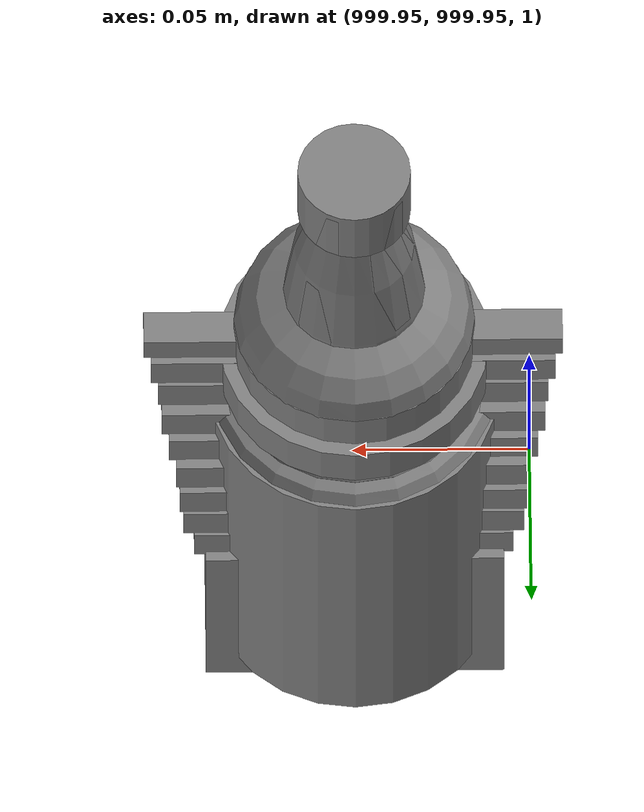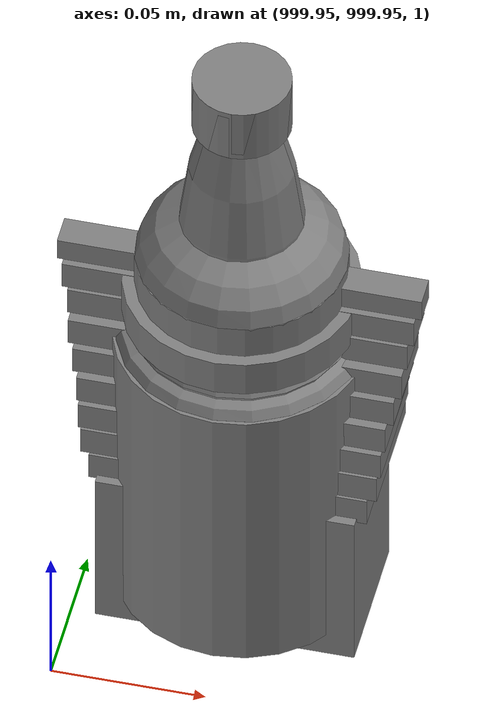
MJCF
<mujoco>
    <option gravity="0.000000000 0.000000000 -9.810000420" timestep="0.0166666" integrator="implicitfast" density="1.225" viscosity="1.8000001e-05" noslip_iterations="10" iterations="100" sdf_iterations="50">
        <flag multiccd="disable"/>
    </option>
    <size memory="1000M"/>
    <compiler coordinate="local"/>
    <worldbody>
        <light cutoff="30" pos="0 1 1" dir="0 -1 -2"/>
        <light cutoff="30" pos="0 -1 1" dir="0 1 -2"/>
        <body pos="-7.168000221 2.823999882 1.227496982" euler="-0.283413976 0.056829724 -0.133293271" name="openloong_gripper_2f85_fix_base_usda_Pos">
            <geom contype="1" conaffinity="1" density="1000" type="box" material="" rgba="0.500000000 0.500000000 0.500000000 1.000000000" solimp="0.899999976 0.949999988 0.001000000" friction="1.000000000 0.005000000 0.000100000" solref="0.020000000 1.000000000" margin="0" condim="3" group="0" pos="-0.002278805 0.074524641 -0.004134059" quat="0.315989345 0.948763072 -0.000000000 0.000000000" size="0.059999999 0.013000000 0.035000000" name="openloong_gripper_2f85_fix_base_usda_geom_CF04CB96_BD24_4D2F_8271_A35987848B84"/>
            <geom contype="1" conaffinity="1" density="1000" type="box" material="" rgba="0.500000000 0.500000000 0.500000000 1.000000000" solimp="0.899999976 0.949999988 0.001000000" friction="1.000000000 0.005000000 0.000100000" solref="0.020000000 1.000000000" margin="0" condim="3" group="0" pos="-0.002278805 0.078031301 0.008128285" quat="0.990447521 -0.137893379 -0.000000000 -0.000000000" size="0.059999999 0.010000000 0.035000000" name="openloong_gripper_2f85_fix_base_usda_geom_3D52E318_965E_40ED_8670_DC3F22E30BC9"/>
            <geom contype="1" conaffinity="1" density="1000" type="box" material="" rgba="0.500000000 0.500000000 0.500000000 1.000000000" solimp="0.899999976 0.949999988 0.001000000" friction="1.000000000 0.005000000 0.000100000" solref="0.020000000 1.000000000" margin="0" condim="3" group="0" pos="-0.002278805 0.080785275 -0.002596974" quat="0.287325472 -0.957833409 0.000000000 -0.000000000" size="0.059999999 0.013000000 0.035000000" name="openloong_gripper_2f85_fix_base_usda_geom_B20FE257_FC12_40EF_9148_6B1D69C1029C"/>
            <geom contype="1" conaffinity="1" density="1000" type="box" material="" rgba="0.500000000 0.500000000 0.500000000 1.000000000" solimp="0.899999976 0.949999988 0.001000000" friction="1.000000000 0.005000000 0.000100000" solref="0.020000000 1.000000000" margin="0" condim="3" group="0" pos="-0.002278805 -0.098804474 -0.020146966" quat="0.988851666 0.148906454 0.000000000 -0.000000000" size="0.059999999 0.022000000 0.020000000" name="openloong_gripper_2f85_fix_base_usda_geom_04DA59F3_188B_48C5_A173_6CF2D2867227"/>
            <geom contype="1" conaffinity="1" density="1000" type="box" material="" rgba="0.500000000 0.500000000 0.500000000 1.000000000" solimp="0.899999976 0.949999988 0.001000000" friction="1.000000000 0.005000000 0.000100000" solref="0.020000000 1.000000000" margin="0" condim="3" group="0" pos="-0.002279282 0.019920111 0.012102962" quat="0.995421767 0.095583342 -0.000000000 -0.000000000" size="0.059999999 0.025000000 0.026000001" name="openloong_gripper_2f85_fix_base_usda_geom_D4E21CC0_9F0C_46DD_A2CD_6F3254786C3B"/>
            <geom contype="1" conaffinity="1" density="1000" type="box" material="" rgba="0.500000000 0.500000000 0.500000000 1.000000000" solimp="0.899999976 0.949999988 0.001000000" friction="1.000000000 0.005000000 0.000100000" solref="0.020000000 1.000000000" margin="0" condim="3" group="0" pos="-0.002279282 0.005734444 -0.014276862" quat="0.999571741 -0.029275302 -0.000000000 -0.000000000" size="0.059999999 0.050000001 0.010000000" name="openloong_gripper_2f85_fix_base_usda_geom_662329F5_598B_4166_9004_9E3D9ED068FF"/>
            <geom contype="1" conaffinity="1" density="1000" type="box" material="" rgba="0.500000000 0.500000000 0.500000000 1.000000000" solimp="0.899999976 0.949999988 0.001000000" friction="1.000000000 0.005000000 0.000100000" solref="0.020000000 1.000000000" margin="0" condim="3" group="0" pos="-0.002278805 0.079460382 0.007771969" quat="0.922590554 -0.385781586 0.000000000 -0.000000000" size="0.059999999 0.010000000 0.035000000" name="openloong_gripper_2f85_fix_base_usda_geom_18610BF1_437C_4C9B_8F17_DD0982F40635"/>
            <geom contype="1" conaffinity="1" density="1000" type="box" material="" rgba="0.500000000 0.500000000 0.500000000 1.000000000" solimp="0.899999976 0.949999988 0.001000000" friction="1.000000000 0.005000000 0.000100000" solref="0.020000000 1.000000000" margin="0" condim="3" group="0" pos="-0.002279282 0.081384182 -0.001320124" quat="0.590483785 -0.807049930 0.000000000 -0.000000000" size="0.059999999 0.013000000 0.035000000" name="openloong_gripper_2f85_fix_base_usda_geom_98BCD84B_DA74_46D7_AB63_64FC3075D2B1"/>
            <geom contype="1" conaffinity="1" density="1000" type="box" material="" rgba="0.500000000 0.500000000 0.500000000 1.000000000" solimp="0.899999976 0.949999988 0.001000000" friction="1.000000000 0.005000000 0.000100000" solref="0.020000000 1.000000000" margin="0" condim="3" group="0" pos="-0.002278805 -0.059297800 -0.007972836" quat="0.988851666 0.148906454 0.000000000 -0.000000000" size="0.059999999 0.020000000 0.022000000" name="openloong_gripper_2f85_fix_base_usda_geom_86286F8E_80B8_46E2_A9CB_CB3609F02636"/>
            <geom contype="1" conaffinity="1" density="1000" type="box" material="" rgba="0.500000000 0.500000000 0.500000000 1.000000000" solimp="0.899999976 0.949999988 0.001000000" friction="1.000000000 0.005000000 0.000100000" solref="0.020000000 1.000000000" margin="0" condim="3" group="0" pos="-0.002278805 0.076618671 -0.004656792" quat="0.004634961 0.999989629 -0.000000000 0.000000000" size="0.059999999 0.013000000 0.035000000" name="openloong_gripper_2f85_fix_base_usda_geom_F84C97A9_8719_402C_9EB7_062202E3B742"/>
            <geom contype="1" conaffinity="1" density="1000" type="box" material="" rgba="0.500000000 0.500000000 0.500000000 1.000000000" solimp="0.899999976 0.949999988 0.001000000" friction="1.000000000 0.005000000 0.000100000" solref="0.020000000 1.000000000" margin="0" condim="3" group="0" pos="-0.002279282 -0.021952629 0.002960086" quat="0.991270423 0.131847665 -0.000000000 0.000000000" size="0.059999999 0.020000000 0.024000000" name="openloong_gripper_2f85_fix_base_usda_geom_33DE7D72_6AD3_4EF9_9354_D5AA401C210A"/>
            <geom contype="1" conaffinity="1" density="1000" type="box" material="" rgba="0.500000000 0.500000000 0.500000000 1.000000000" solimp="0.899999976 0.949999988 0.001000000" friction="1.000000000 0.005000000 0.000100000" solref="0.020000000 1.000000000" margin="0" condim="3" group="0" pos="-0.002278805 0.081418991 0.002587914" quat="0.803492308 -0.595315695 0.000000000 -0.000000000" size="0.059999999 0.013000000 0.035000000" name="openloong_gripper_2f85_fix_base_usda_geom_2DA24F24_6211_48FC_BD40_9988D72E17A7"/>
            <geom contype="1" conaffinity="1" density="1000" type="box" material="" rgba="0.500000000 0.500000000 0.500000000 1.000000000" solimp="0.899999976 0.949999988 0.001000000" friction="1.000000000 0.005000000 0.000100000" solref="0.020000000 1.000000000" margin="0" condim="3" group="0" pos="-0.002278805 0.061115503 0.008545756" quat="0.999326169 0.036714450 0.000000000 -0.000000000" size="0.059999999 0.020000000 0.035000000" name="openloong_gripper_2f85_fix_base_usda_geom_AC85CDFD_59A9_4293_81BE_C9BDA7C834CD"/>
            <freejoint name="openloong_gripper_2f85_fix_base_usda_pos_scan"/>
        </body>
        <body pos="1000.000000000 1000.000000000 1.000000000" euler="0.000000000 0.000000000 0.000000000" name="openloong_gripper_2f85_fix_base_usda_bottle_red">
            <geom contype="1" conaffinity="1" density="1000" type="ellipsoid" material="" rgba="0.500000000 0.500000000 0.500000000 1.000000000" solimp="0.899999976 0.949999988 0.001000000" friction="1.000000000 0.005000000 0.000100000" solref="0.020000000 1.000000000" margin="0" condim="3" group="0" pos="0.000000000 0.000000000 0.144284487" quat="1.000000000 0.000000000 0.000000000 0.000000000" size="0.021000000 0.021000000 0.079999998" name="openloong_gripper_2f85_fix_base_usda_geom_AEE48C65_BCB6_4B17_8806_2776B827279A"/>
            <geom contype="1" conaffinity="1" density="1000" type="cylinder" material="" rgba="0.500000000 0.500000000 0.500000000 1.000000000" solimp="0.899999976 0.949999988 0.001000000" friction="1.000000000 0.005000000 0.000100000" solref="0.020000000 1.000000000" margin="0" condim="3" group="0" pos="0.000000000 0.000000000 0.220618963" quat="1.000000000 0.000000000 0.000000000 0.000000000" size="0.016000001 0.010000000 1.000000000" name="openloong_gripper_2f85_fix_base_usda_geom_2473292B_863C_4063_93A8_5690E8D5A5B2"/>
            <geom contype="1" conaffinity="1" density="1000" type="ellipsoid" material="" rgba="0.500000000 0.500000000 0.500000000 1.000000000" solimp="0.899999976 0.949999988 0.001000000" friction="1.000000000 0.005000000 0.000100000" solref="0.020000000 1.000000000" margin="0" condim="3" group="0" pos="0.000000000 0.000000000 0.118945479" quat="1.000000000 0.000000000 0.000000000 0.000000000" size="0.030999999 0.030999999 0.029999999" name="openloong_gripper_2f85_fix_base_usda_geom_E52843CC_634A_4E1D_8996_5154AA835B59"/>
            <geom contype="1" conaffinity="1" density="1000" type="box" material="" rgba="0.500000000 0.500000000 0.500000000 1.000000000" solimp="0.899999976 0.949999988 0.001000000" friction="1.000000000 0.005000000 0.000100000" solref="0.020000000 1.000000000" margin="0" condim="3" group="0" pos="0.000000000 0.000000000 0.002189159" quat="1.000000000 0.000000000 0.000000000 0.000000000" size="0.020000000 0.020000000 0.003000000" name="openloong_gripper_2f85_fix_base_usda_geom_15B90AF9_3218_4316_91FD_67147BFC0AEC"/>
            <geom contype="1" conaffinity="1" density="1000" type="cylinder" material="" rgba="0.500000000 0.500000000 0.500000000 1.000000000" solimp="0.899999976 0.949999988 0.001000000" friction="1.000000000 0.005000000 0.000100000" solref="0.020000000 1.000000000" margin="0" condim="3" group="0" pos="0.000000000 -0.000366211 0.060884237" quat="1.000000000 0.000000000 0.000000000 0.000000000" size="0.030999999 0.057999998 1.000000000" name="openloong_gripper_2f85_fix_base_usda_geom_BD816386_53B6_4FAF_AA67_73FC1BD29EC3"/>
            <freejoint name="openloong_gripper_2f85_fix_base_usda_bottle_red_joint"/>
            <site size="0.005000000 0.005000000 0.005000000" rgba="0.500000000 0.500000000 0.500000000 1.000000000" pos="0.000000000 0.000000000 0.000000000" quat="0.999961913 0.008726535 0.000000000 0.000000000" group="0" type="sphere" name="openloong_gripper_2f85_fix_base_usda_bottle_redsite"/>
        </body>
        <body pos="1000.000000000 1000.000000000 1.000000000" euler="0.000000000 0.000000000 0.000000000" name="openloong_gripper_2f85_fix_base_usda_bottle_blue">
            <geom contype="1" conaffinity="1" density="1000" type="ellipsoid" material="" rgba="0.500000000 0.500000000 0.500000000 1.000000000" solimp="0.899999976 0.949999988 0.001000000" friction="1.000000000 0.005000000 0.000100000" solref="0.020000000 1.000000000" margin="0" condim="3" group="0" pos="0.000000000 0.000000000 0.118920922" quat="1.000000000 0.000000000 0.000000000 0.000000000" size="0.030999999 0.030999999 0.029999999" name="openloong_gripper_2f85_fix_base_usda_geom_E5F456C6_EEFA_4B52_AF27_0DF43992BD50"/>
            <geom contype="1" conaffinity="1" density="1000" type="box" material="" rgba="0.500000000 0.500000000 0.500000000 1.000000000" solimp="0.899999976 0.949999988 0.001000000" friction="1.000000000 0.005000000 0.000100000" solref="0.020000000 1.000000000" margin="0" condim="3" group="0" pos="0.000000000 0.000000000 0.002164602" quat="1.000000000 0.000000000 0.000000000 0.000000000" size="0.020000000 0.020000000 0.003000000" name="openloong_gripper_2f85_fix_base_usda_geom_2A320682_7C3B_4485_B5E2_5D466AAB3E9D"/>
            <geom contype="1" conaffinity="1" density="1000" type="cylinder" material="" rgba="0.500000000 0.500000000 0.500000000 1.000000000" solimp="0.899999976 0.949999988 0.001000000" friction="1.000000000 0.005000000 0.000100000" solref="0.020000000 1.000000000" margin="0" condim="3" group="0" pos="0.000000000 -0.000366211 0.060859680" quat="1.000000000 0.000000000 0.000000000 0.000000000" size="0.030999999 0.057999998 1.000000000" name="openloong_gripper_2f85_fix_base_usda_geom_473E2FA4_6F56_4028_861F_50757A220772"/>
            <geom contype="1" conaffinity="1" density="1000" type="cylinder" material="" rgba="0.500000000 0.500000000 0.500000000 1.000000000" solimp="0.899999976 0.949999988 0.001000000" friction="1.000000000 0.005000000 0.000100000" solref="0.020000000 1.000000000" margin="0" condim="3" group="0" pos="0.000000000 0.000000000 0.220594406" quat="1.000000000 0.000000000 0.000000000 0.000000000" size="0.016000001 0.010000000 1.000000000" name="openloong_gripper_2f85_fix_base_usda_geom_395F33B7_60BE_4573_89E6_AAA3217DB42E"/>
            <geom contype="1" conaffinity="1" density="1000" type="ellipsoid" material="" rgba="0.500000000 0.500000000 0.500000000 1.000000000" solimp="0.899999976 0.949999988 0.001000000" friction="1.000000000 0.005000000 0.000100000" solref="0.020000000 1.000000000" margin="0" condim="3" group="0" pos="0.000000000 0.000000000 0.144259930" quat="1.000000000 0.000000000 0.000000000 0.000000000" size="0.021000000 0.021000000 0.079999998" name="openloong_gripper_2f85_fix_base_usda_geom_6D00FA6B_706A_4984_B622_043FB541AB0A"/>
            <freejoint name="openloong_gripper_2f85_fix_base_usda_bottle_blue_joint"/>
            <site size="0.005000000 0.005000000 0.005000000" rgba="0.500000000 0.500000000 0.500000000 1.000000000" pos="0.000000000 0.000000000 0.000000000" quat="0.999961913 0.008726535 0.000000000 0.000000000" group="0" type="sphere" name="openloong_gripper_2f85_fix_base_usda_bottle_bluesite"/>
        </body>
        <body pos="-2.075402260 6.227426052 1.735658646" euler="-110.827117920 51.151107788 -43.520626068" mocap="true" name="spotlight2_SpotLight"/>
        <body pos="-1.937217832 5.723894119 1.802600980" euler="142.838195801 -45.959964752 -39.684494019" mocap="true" name="spotlight4_SpotLight"/>
        <body pos="1000.000000000 1000.000000000 1.000000000" euler="0.000000000 0.000000000 0.000000000" name="openloong_gripper_2f85_fix_base_usda_jar_01">
            <geom contype="1" conaffinity="1" density="1000" type="box" material="" rgba="0.500000000 0.500000000 0.500000000 1.000000000" solimp="0.899999976 0.949999988 0.001000000" friction="1.000000000 0.005000000 0.000100000" solref="0.020000000 1.000000000" margin="0" condim="3" group="0" pos="0.000000000 0.000000000 0.006158113" quat="1.000000000 0.000000000 0.000000000 0.000000000" size="0.020000000 0.020000000 0.005000000" name="openloong_gripper_2f85_fix_base_usda_geom_33F99860_47A4_4454_9110_B03B12597353"/>
            <geom contype="1" conaffinity="1" density="1000" type="cylinder" material="" rgba="0.500000000 0.500000000 0.500000000 1.000000000" solimp="0.899999976 0.949999988 0.001000000" friction="1.000000000 0.005000000 0.000100000" solref="0.020000000 1.000000000" margin="0" condim="3" group="0" pos="0.000000000 0.000000000 0.062744498" quat="1.000000000 0.000000000 0.000000000 0.000000000" size="0.041000001 0.052999999 1.000000000" name="openloong_gripper_2f85_fix_base_usda_geom_D6572A57_1B41_48CB_8D17_BEC8D8723F65"/>
            <geom contype="1" conaffinity="1" density="1000" type="ellipsoid" material="" rgba="0.500000000 0.500000000 0.500000000 1.000000000" solimp="0.899999976 0.949999988 0.001000000" friction="1.000000000 0.005000000 0.000100000" solref="0.020000000 1.000000000" margin="0" condim="3" group="0" pos="0.000000000 0.000000000 0.122252703" quat="1.000000000 0.000000000 0.000000000 0.000000000" size="0.035999998 0.035999998 0.010000000" name="openloong_gripper_2f85_fix_base_usda_geom_CBA26805_F3B4_4C85_B236_33E3957D369F"/>
            <geom contype="1" conaffinity="1" density="1000" type="cylinder" material="" rgba="0.500000000 0.500000000 0.500000000 1.000000000" solimp="0.899999976 0.949999988 0.001000000" friction="1.000000000 0.005000000 0.000100000" solref="0.020000000 1.000000000" margin="0" condim="3" group="0" pos="0.000000000 0.000000000 0.015747190" quat="1.000000000 0.000000000 0.000000000 0.000000000" size="0.035000000 0.010000000 1.000000000" name="openloong_gripper_2f85_fix_base_usda_geom_C81D9B37_4D77_4F7A_AA41_38455D668CD4"/>
            <geom contype="1" conaffinity="1" density="1000" type="ellipsoid" material="" rgba="0.500000000 0.500000000 0.500000000 1.000000000" solimp="0.899999976 0.949999988 0.001000000" friction="1.000000000 0.005000000 0.000100000" solref="0.020000000 1.000000000" margin="0" condim="3" group="0" pos="0.000000000 0.000000000 0.115815401" quat="1.000000000 0.000000000 0.000000000 0.000000000" size="0.039999999 0.039999999 0.010000000" name="openloong_gripper_2f85_fix_base_usda_geom_B80C821F_D05A_42BB_8DFA_3690BAFDC943"/>
            <geom contype="1" conaffinity="1" density="1000" type="cylinder" material="" rgba="0.500000000 0.500000000 0.500000000 1.000000000" solimp="0.899999976 0.949999988 0.001000000" friction="1.000000000 0.005000000 0.000100000" solref="0.020000000 1.000000000" margin="0" condim="3" group="0" pos="0.000000000 0.000000000 0.133183479" quat="1.000000000 0.000000000 0.000000000 0.000000000" size="0.037999999 0.006500000 1.000000000" name="openloong_gripper_2f85_fix_base_usda_geom_11A26F94_2620_4D2F_A464_E682F322D995"/>
            <freejoint name="openloong_gripper_2f85_fix_base_usda_jar_01_joint"/>
            <site size="0.005000000 0.005000000 0.005000000" rgba="0.500000000 0.500000000 0.500000000 1.000000000" pos="0.000000000 0.000000000 0.000000000" quat="1.000000000 0.000000000 0.000000000 0.000000000" group="0" type="sphere" name="openloong_gripper_2f85_fix_base_usda_jar_01site"/>
        </body>
        <body pos="1000.000000000 1000.000000000 1.000000000" euler="0.000000000 0.000000000 0.000000000" name="openloong_gripper_2f85_fix_base_usda_salt">
            <geom contype="1" conaffinity="1" density="1000" type="box" material="" rgba="0.500000000 0.500000000 0.500000000 1.000000000" solimp="0.899999976 0.949999988 0.001000000" friction="1.000000000 0.005000000 0.000100000" solref="0.020000000 1.000000000" margin="0" condim="3" group="0" pos="0.000305176 0.000000000 0.084862232" quat="1.000000000 0.000000000 0.000000000 0.000000000" size="0.048999999 0.018999999 0.005000000" name="openloong_gripper_2f85_fix_base_usda_geom_5B3A6A2C_A76F_4087_8F65_C916523E7672"/>
            <geom contype="1" conaffinity="1" density="1000" type="box" material="" rgba="0.500000000 0.500000000 0.500000000 1.000000000" solimp="0.899999976 0.949999988 0.001000000" friction="1.000000000 0.005000000 0.000100000" solref="0.020000000 1.000000000" margin="0" condim="3" group="0" pos="0.000305176 0.000000000 0.104564309" quat="1.000000000 0.000000000 0.000000000 0.000000000" size="0.052000001 0.014000000 0.005000000" name="openloong_gripper_2f85_fix_base_usda_geom_B09C05D9_8286_4E98_BDCB_EC6384382CB5"/>
            <geom contype="1" conaffinity="1" density="1000" type="box" material="" rgba="0.500000000 0.500000000 0.500000000 1.000000000" solimp="0.899999976 0.949999988 0.001000000" friction="1.000000000 0.005000000 0.000100000" solref="0.020000000 1.000000000" margin="0" condim="3" group="0" pos="0.000305176 0.000000000 0.114487171" quat="1.000000000 0.000000000 0.000000000 0.000000000" size="0.054000001 0.011500000 0.005000000" name="openloong_gripper_2f85_fix_base_usda_geom_C13B9C7A_1582_4F81_8BB3_44D98FE907B0"/>
            <geom contype="1" conaffinity="1" density="1000" type="box" material="" rgba="0.500000000 0.500000000 0.500000000 1.000000000" solimp="0.899999976 0.949999988 0.001000000" friction="1.000000000 0.005000000 0.000100000" solref="0.020000000 1.000000000" margin="0" condim="3" group="0" pos="0.000305176 0.000000000 0.075103164" quat="1.000000000 0.000000000 0.000000000 0.000000000" size="0.048000000 0.020000000 0.005000000" name="openloong_gripper_2f85_fix_base_usda_geom_BC0652DE_E191_4D10_9A18_0F455F32D646"/>
            <geom contype="1" conaffinity="1" density="1000" type="box" material="" rgba="0.500000000 0.500000000 0.500000000 1.000000000" solimp="0.899999976 0.949999988 0.001000000" friction="1.000000000 0.005000000 0.000100000" solref="0.020000000 1.000000000" margin="0" condim="3" group="0" pos="0.000305176 0.000000000 0.134892464" quat="1.000000000 0.000000000 0.000000000 0.000000000" size="0.057000000 0.007000000 0.005000000" name="openloong_gripper_2f85_fix_base_usda_geom_2BCF189C_4EE3_4EBD_A25E_8ECCA77BE4AB"/>
            <geom contype="1" conaffinity="1" density="1000" type="box" material="" rgba="0.500000000 0.500000000 0.500000000 1.000000000" solimp="0.899999976 0.949999988 0.001000000" friction="1.000000000 0.005000000 0.000100000" solref="0.020000000 1.000000000" margin="0" condim="3" group="0" pos="0.000305176 0.000000000 0.094920278" quat="1.000000000 0.000000000 0.000000000 0.000000000" size="0.050000001 0.017000001 0.005000000" name="openloong_gripper_2f85_fix_base_usda_geom_15AF8D26_E705_44E4_86D6_F594CD0E2EEB"/>
            <geom contype="1" conaffinity="1" density="1000" type="box" material="" rgba="0.500000000 0.500000000 0.500000000 1.000000000" solimp="0.899999976 0.949999988 0.001000000" friction="1.000000000 0.005000000 0.000100000" solref="0.020000000 1.000000000" margin="0" condim="3" group="0" pos="0.000305176 0.000000000 0.065204859" quat="1.000000000 0.000000000 0.000000000 0.000000000" size="0.045000002 0.021000000 0.005000000" name="openloong_gripper_2f85_fix_base_usda_geom_79741B26_2F9D_4D34_901A_F54012926969"/>
            <geom contype="1" conaffinity="1" density="1000" type="box" material="" rgba="0.500000000 0.500000000 0.500000000 1.000000000" solimp="0.899999976 0.949999988 0.001000000" friction="1.000000000 0.005000000 0.000100000" solref="0.020000000 1.000000000" margin="0" condim="3" group="0" pos="0.000305176 0.000000000 0.144135714" quat="1.000000000 0.000000000 0.000000000 0.000000000" size="0.059000000 0.005000000 0.004000000" name="openloong_gripper_2f85_fix_base_usda_geom_849B4219_BFE3_40FC_A3ED_72155CF3E596"/>
            <geom contype="1" conaffinity="1" density="1000" type="box" material="" rgba="0.500000000 0.500000000 0.500000000 1.000000000" solimp="0.899999976 0.949999988 0.001000000" friction="1.000000000 0.005000000 0.000100000" solref="0.020000000 1.000000000" margin="0" condim="3" group="0" pos="0.000000000 0.000000000 0.031593561" quat="1.000000000 0.000000000 0.000000000 0.000000000" size="0.041999999 0.024000000 0.029999999" name="openloong_gripper_2f85_fix_base_usda_geom_F5A67A16_2BEB_4F4A_8E9B_59D54CCDB84D"/>
            <geom contype="1" conaffinity="1" density="1000" type="box" material="" rgba="0.500000000 0.500000000 0.500000000 1.000000000" solimp="0.899999976 0.949999988 0.001000000" friction="1.000000000 0.005000000 0.000100000" solref="0.020000000 1.000000000" margin="0" condim="3" group="0" pos="0.000305176 0.000000000 0.124608755" quat="1.000000000 0.000000000 0.000000000 0.000000000" size="0.055000000 0.008000000 0.005000000" name="openloong_gripper_2f85_fix_base_usda_geom_8DD88250_E35E_48C0_8AC1_B315456A3145"/>
            <freejoint name="openloong_gripper_2f85_fix_base_usda_salt_joint"/>
            <site size="0.005000000 0.005000000 0.005000000" rgba="0.500000000 0.500000000 0.500000000 1.000000000" pos="0.000000000 0.000000000 0.000000000" quat="1.000000000 0.000000000 0.000000000 0.000000000" group="0" type="sphere" name="openloong_gripper_2f85_fix_base_usda_saltsite"/>
        </body>
        <body pos="-2.121263981 5.688931465 1.788462281" euler="-76.883239746 36.777637482 2.700538874" mocap="true" name="spotlight3_SpotLight"/>
        <body pos="1000.000000000 1000.000000000 1.000000000" euler="0.000000000 0.000000000 0.000000000" name="openloong_gripper_2f85_fix_base_usda_can">
            <geom contype="1" conaffinity="1" density="1000" type="cylinder" material="" rgba="0.500000000 0.500000000 0.500000000 1.000000000" solimp="0.899999976 0.949999988 0.001000000" friction="1.000000000 0.005000000 0.000100000" solref="0.020000000 1.000000000" margin="0" condim="3" group="0" pos="0.000000000 0.000000000 0.079676986" quat="1.000000000 0.000000000 0.000000000 0.000000000" size="0.034000002 0.071999997 1.000000000" name="openloong_gripper_2f85_fix_base_usda_geom_D370246D_A425_495F_8013_7C2FC90BA5F9"/>
            <geom contype="1" conaffinity="1" density="1000" type="ellipsoid" material="" rgba="0.500000000 0.500000000 0.500000000 1.000000000" solimp="0.899999976 0.949999988 0.001000000" friction="1.000000000 0.005000000 0.000100000" solref="0.020000000 1.000000000" margin="0" condim="3" group="0" pos="0.000000000 0.000000000 0.151854277" quat="1.000000000 0.000000000 0.000000000 0.000000000" size="0.034000002 0.034000002 0.020000000" name="openloong_gripper_2f85_fix_base_usda_geom_8A68F30D_3DB1_4ADF_9904_43F77215A294"/>
            <geom contype="1" conaffinity="1" density="1000" type="box" material="" rgba="0.500000000 0.500000000 0.500000000 1.000000000" solimp="0.899999976 0.949999988 0.001000000" friction="1.000000000 0.005000000 0.000100000" solref="0.020000000 1.000000000" margin="0" condim="3" group="0" pos="0.000000000 0.000000000 0.004777670" quat="1.000000000 0.000000000 0.000000000 0.000000000" size="0.020000000 0.020000000 0.005000000" name="openloong_gripper_2f85_fix_base_usda_geom_87E27002_3A6D_41DA_A758_7EB96E070C7A"/>
            <freejoint name="openloong_gripper_2f85_fix_base_usda_can_joint"/>
            <site size="0.005000000 0.005000000 0.005000000" rgba="0.500000000 0.500000000 0.500000000 1.000000000" pos="0.000000000 0.000000000 0.000000000" quat="1.000000000 0.000000000 0.000000000 0.000000000" group="0" type="sphere" name="openloong_gripper_2f85_fix_base_usda_cansite"/>
        </body>
        <body pos="0.000000000 0.000000000 0.000000000" euler="0.000000000 0.000000000 0.000000000" name=" Static Objects_ Static Objects">
            <geom contype="1" conaffinity="1" density="1000" type="box" material="" rgba="0.500000000 0.500000000 0.500000000 1.000000000" solimp="0.899999976 0.949999988 0.001000000" friction="1.000000000 0.005000000 0.000100000" solref="0.020000000 1.000000000" margin="0" condim="3" group="0" pos="-6.460197449 2.937205315 0.548931718" quat="1.000000000 0.000000000 0.000000000 0.000000000" size="2.650000095 0.430000007 0.550000012" name=" Static Objects_geom_E4274E38_5A71_4910_89CD_CFA6611ABDB9"/>
            <geom contype="1" conaffinity="1" density="1000" type="box" material="" rgba="0.500000000 0.500000000 0.500000000 1.000000000" solimp="0.899999976 0.949999988 0.001000000" friction="1.000000000 0.005000000 0.000100000" solref="0.020000000 1.000000000" margin="0" condim="3" group="0" pos="-4.240264893 1.327049494 0.549888909" quat="1.000000000 0.000000000 0.000000000 0.000000000" size="0.430000007 1.200000048 0.550000012" name=" Static Objects_geom_683A21A0_3FA7_4CEA_ABA1_C2290F5FA0C7"/>
            <geom contype="1" conaffinity="1" density="1000" type="box" material="" rgba="0.500000000 0.500000000 0.500000000 1.000000000" solimp="0.899999976 0.949999988 0.001000000" friction="1.000000000 0.005000000 0.000100000" solref="0.020000000 1.000000000" margin="0" condim="3" group="0" pos="-8.830721855 2.096410990 0.549305558" quat="1.000000000 0.000000000 0.000000000 0.000000000" size="0.280000001 0.430000007 0.550000012" name=" Static Objects_geom_F3C98334_D28C_4FEF_9531_84462E46A40D"/>
            <geom contype="1" conaffinity="1" density="1000" type="box" material="" rgba="0.500000000 0.500000000 0.500000000 1.000000000" solimp="0.899999976 0.949999988 0.001000000" friction="1.000000000 0.005000000 0.000100000" solref="0.020000000 1.000000000" margin="0" condim="3" group="0" pos="-7.408766270 3.088089943 1.776644945" quat="0.928051054 0.000000000 0.000000000 0.372453064" size="0.050000001 0.100000001 0.050000001" name=" Static Objects_geom_80208F92_56B0_4059_9E09_8BDA20B1A51B"/>
            <geom contype="1" conaffinity="1" density="1000" type="box" material="" rgba="0.500000000 0.500000000 0.500000000 1.000000000" solimp="0.899999976 0.949999988 0.001000000" friction="1.000000000 0.005000000 0.000100000" solref="0.020000000 1.000000000" margin="0" condim="3" group="0" pos="-7.719123363 2.867671013 1.173410416" quat="1.000000000 0.000000000 0.000000000 0.000000000" size="0.250000000 0.250000000 0.079999998" name=" Static Objects_geom_0B96C520_17FB_4A6F_9605_077F3038DE29"/>
            <geom contype="1" conaffinity="1" density="1000" type="box" material="" rgba="0.500000000 0.500000000 0.500000000 1.000000000" solimp="0.899999976 0.949999988 0.001000000" friction="1.000000000 0.005000000 0.000100000" solref="0.020000000 1.000000000" margin="0" condim="3" group="0" pos="-7.437745571 3.067511320 1.289965630" quat="1.000000000 0.000000000 0.000000000 0.000000000" size="0.029999999 0.020000000 0.020000000" name=" Static Objects_geom_BD8B4F0E_EB85_4C5C_8669_1DD106F78AB6"/>
            <geom contype="1" conaffinity="1" density="1000" type="box" material="" rgba="0.500000000 0.500000000 0.500000000 1.000000000" solimp="0.899999976 0.949999988 0.001000000" friction="1.000000000 0.005000000 0.000100000" solref="0.020000000 1.000000000" margin="0" condim="3" group="0" pos="-7.719123363 2.958004713 1.530241251" quat="1.000000000 0.000000000 0.000000000 0.000000000" size="0.250000000 0.159999996 0.280000001" name=" Static Objects_geom_6CBE1DE7_4F72_4951_B6C6_BC3D8F4B6AF3"/>
            <geom contype="1" conaffinity="1" density="1000" type="cylinder" material="" rgba="0.500000000 0.500000000 0.500000000 1.000000000" solimp="0.899999976 0.949999988 0.001000000" friction="1.000000000 0.005000000 0.000100000" solref="0.020000000 1.000000000" margin="0" condim="3" group="0" pos="-7.427312374 3.069516420 1.502544641" quat="0.928051054 0.000000000 0.000000000 0.372453064" size="0.015000000 0.230000004 0.100000001" name=" Static Objects_geom_1FCC69A1_7D5F_4ABF_BB56_19E07B02C269"/>
            <geom contype="1" conaffinity="1" density="1000" type="box" material="" rgba="0.500000000 0.500000000 0.500000000 1.000000000" solimp="0.899999976 0.949999988 0.001000000" friction="1.000000000 0.005000000 0.000100000" solref="0.020000000 1.000000000" margin="0" condim="3" group="0" pos="-2.825197220 6.153595448 1.563861728" quat="0.707107067 0.000000000 0.000000000 0.707106471" size="0.550000012 0.239999995 0.025000000" name=" Static Objects_geom_9B0CD456_33AB_45A9_A3E9_7A77C194BC3D"/>
            <geom contype="1" conaffinity="1" density="1000" type="box" material="" rgba="0.500000000 0.500000000 0.500000000 1.000000000" solimp="0.899999976 0.949999988 0.001000000" friction="1.000000000 0.005000000 0.000100000" solref="0.020000000 1.000000000" margin="0" condim="3" group="0" pos="-6.311686516 6.153595448 1.018643856" quat="0.707107067 0.000000000 0.000000000 0.707106471" size="0.050000001 3.150000095 1.019999981" name=" Static Objects_geom_AB2F8798_648D_482C_A325_03779F7802CB"/>
            <geom contype="1" conaffinity="1" density="1000" type="box" material="" rgba="0.500000000 0.500000000 0.500000000 1.000000000" solimp="0.899999976 0.949999988 0.001000000" friction="1.000000000 0.005000000 0.000100000" solref="0.020000000 1.000000000" margin="0" condim="3" group="0" pos="-6.286010742 6.153595448 0.096129179" quat="0.707107067 0.000000000 0.000000000 0.707106471" size="0.529999971 3.134999990 0.098999999" name=" Static Objects_geom_1EC4D7FA_8034_4E40_97AD_7365A9F232FF"/>
            <geom contype="1" conaffinity="1" density="1000" type="box" material="" rgba="0.500000000 0.500000000 0.500000000 1.000000000" solimp="0.899999976 0.949999988 0.001000000" friction="1.000000000 0.005000000 0.000100000" solref="0.020000000 1.000000000" margin="0" condim="3" group="0" pos="-2.825197220 6.153595448 1.115278244" quat="0.707107067 0.000000000 0.000000000 0.707106471" size="0.550000012 0.239999995 0.025000000" name=" Static Objects_geom_5315BEBC_2AFC_44B1_96C7_6C20D454E744"/>
            <geom contype="1" conaffinity="1" density="1000" type="box" material="" rgba="0.500000000 0.500000000 0.500000000 1.000000000" solimp="0.899999976 0.949999988 0.001000000" friction="1.000000000 0.005000000 0.000100000" solref="0.020000000 1.000000000" margin="0" condim="3" group="0" pos="-2.825197220 6.153595448 0.097434282" quat="0.707107067 0.000000000 0.000000000 0.707106471" size="0.550000012 0.239999995 0.098999999" name=" Static Objects_geom_38D33AB9_A549_497B_BA35_CD4650EC0A7D"/>
            <geom contype="1" conaffinity="1" density="1000" type="box" material="" rgba="0.500000000 0.500000000 0.500000000 1.000000000" solimp="0.899999976 0.949999988 0.001000000" friction="1.000000000 0.005000000 0.000100000" solref="0.020000000 1.000000000" margin="0" condim="3" group="0" pos="-3.101639986 6.150595188 1.018643856" quat="1.000000000 0.000000000 0.000000000 0.000000000" size="0.050000001 0.579999983 1.019999981" name=" Static Objects_geom_8BF06D69_4F81_48B6_BA22_8B10388BC17B"/>
            <geom contype="1" conaffinity="1" density="1000" type="box" material="" rgba="0.500000000 0.500000000 0.500000000 1.000000000" solimp="0.899999976 0.949999988 0.001000000" friction="1.000000000 0.005000000 0.000100000" solref="0.020000000 1.000000000" margin="0" condim="3" group="0" pos="-6.293097973 6.153595448 1.114443064" quat="0.707107067 0.000000000 0.000000000 0.707106471" size="0.529999971 3.134999990 0.025000000" name=" Static Objects_geom_3D21B8E0_6D42_4F9F_B800_18A669FCC7E6"/>
            <geom contype="1" conaffinity="1" density="1000" type="box" material="" rgba="0.500000000 0.500000000 0.500000000 1.000000000" solimp="0.899999976 0.949999988 0.001000000" friction="1.000000000 0.005000000 0.000100000" solref="0.020000000 1.000000000" margin="0" condim="3" group="0" pos="-2.825197220 6.153595448 0.629031777" quat="0.707107067 0.000000000 0.000000000 0.707106471" size="0.550000012 0.239999995 0.025000000" name=" Static Objects_geom_B7CDB7D4_A426_4F5F_9557_FE5B36B310AE"/>
            <geom contype="1" conaffinity="1" density="1000" type="box" material="" rgba="0.500000000 0.500000000 0.500000000 1.000000000" solimp="0.899999976 0.949999988 0.001000000" friction="1.000000000 0.005000000 0.000100000" solref="0.020000000 1.000000000" margin="0" condim="3" group="0" pos="-6.286010742 6.153595448 1.563861728" quat="0.707107067 0.000000000 0.000000000 0.707106471" size="0.529999971 3.134999990 0.025000000" name=" Static Objects_geom_3BEECF8F_51B9_44B5_8EB2_A1E6ADDD2722"/>
            <geom contype="1" conaffinity="1" density="1000" type="box" material="" rgba="0.500000000 0.500000000 0.500000000 1.000000000" solimp="0.899999976 0.949999988 0.001000000" friction="1.000000000 0.005000000 0.000100000" solref="0.020000000 1.000000000" margin="0" condim="3" group="0" pos="-6.286010742 6.153595448 0.629031777" quat="0.707107067 0.000000000 0.000000000 0.707106471" size="0.529999971 3.134999990 0.025000000" name=" Static Objects_geom_C78E8BE7_A709_48CF_B0B1_4ED0F99C9EA0"/>
            <geom contype="1" conaffinity="1" density="1000" type="box" material="" rgba="0.500000000 0.500000000 0.500000000 1.000000000" solimp="0.899999976 0.949999988 0.001000000" friction="1.000000000 0.005000000 0.000100000" solref="0.020000000 1.000000000" margin="0" condim="3" group="0" pos="-6.824534416 6.447464466 1.212718010" quat="1.000000000 0.000000000 0.000000000 0.000000000" size="0.100000001 0.100000001 0.075000003" name=" Static Objects_geom_D1912303_71A3_4FD3_99D6_F86891A2142C"/>
            <geom contype="1" conaffinity="1" density="1000" type="box" material="" rgba="0.500000000 0.500000000 0.500000000 1.000000000" solimp="0.899999976 0.949999988 0.001000000" friction="1.000000000 0.005000000 0.000100000" solref="0.020000000 1.000000000" margin="0" condim="3" group="0" pos="-9.237723351 6.464855671 1.209077358" quat="1.000000000 0.000000000 0.000000000 0.000000000" size="0.100000001 0.100000001 0.070000000" name=" Static Objects_geom_6984BC8B_8011_4766_9A70_8786802E94DA"/>
            <geom contype="1" conaffinity="1" density="1000" type="box" material="" rgba="0.500000000 0.500000000 0.500000000 1.000000000" solimp="0.899999976 0.949999988 0.001000000" friction="1.000000000 0.005000000 0.000100000" solref="0.020000000 1.000000000" margin="0" condim="3" group="0" pos="-5.611940861 6.318420410 0.350975692" quat="1.000000000 0.000000000 0.000000000 0.000000000" size="0.699999988 0.100000001 0.150000006" name=" Static Objects_geom_454C6C91_BC20_4691_B25A_E4E508682C74"/>
            <geom contype="1" conaffinity="1" density="1000" type="box" material="" rgba="0.500000000 0.500000000 0.500000000 1.000000000" solimp="0.899999976 0.949999988 0.001000000" friction="1.000000000 0.005000000 0.000100000" solref="0.020000000 1.000000000" margin="0" condim="3" group="0" pos="-7.886891365 6.459744930 0.352518857" quat="1.000000000 0.000000000 0.000000000 0.000000000" size="1.500000000 0.200000003 0.150000006" name=" Static Objects_geom_E250CC15_9229_4297_8461_88A8883D0D18"/>
            <geom contype="1" conaffinity="1" density="1000" type="box" material="" rgba="0.500000000 0.500000000 0.500000000 1.000000000" solimp="0.899999976 0.949999988 0.001000000" friction="1.000000000 0.005000000 0.000100000" solref="0.020000000 1.000000000" margin="0" condim="3" group="0" pos="-9.058088303 6.434794426 1.209077358" quat="1.000000000 0.000000000 0.000000000 0.000000000" size="0.250000000 0.100000001 0.070000000" name=" Static Objects_geom_F2757CD6_600D_4976_9E88_FCDD91391286"/>
            <geom contype="1" conaffinity="1" density="1000" type="box" material="" rgba="0.500000000 0.500000000 0.500000000 1.000000000" solimp="0.899999976 0.949999988 0.001000000" friction="1.000000000 0.005000000 0.000100000" solref="0.020000000 1.000000000" margin="0" condim="3" group="0" pos="-7.373087406 6.458900928 1.214329123" quat="1.000000000 0.000000000 0.000000000 0.000000000" size="0.250000000 0.200000003 0.075000003" name=" Static Objects_geom_6D9FABEB_3772_43E5_BD07_64F60650CC70"/>
            <geom contype="1" conaffinity="1" density="1000" type="box" material="" rgba="0.500000000 0.500000000 0.500000000 1.000000000" solimp="0.899999976 0.949999988 0.001000000" friction="1.000000000 0.005000000 0.000100000" solref="0.020000000 1.000000000" margin="0" condim="3" group="0" pos="-6.924745083 6.362090111 1.214329123" quat="1.000000000 0.000000000 0.000000000 0.000000000" size="0.200000003 0.100000001 0.075000003" name=" Static Objects_geom_A60C261D_BB2A_4036_A3A3_25513DB5B0AC"/>
            <geom contype="1" conaffinity="1" density="1000" type="box" material="" rgba="0.500000000 0.500000000 0.500000000 1.000000000" solimp="0.899999976 0.949999988 0.001000000" friction="1.000000000 0.005000000 0.000100000" solref="0.020000000 1.000000000" margin="0" condim="3" group="0" pos="-3.907610416 6.318625927 0.800981164" quat="1.000000000 0.000000000 0.000000000 0.000000000" size="0.500000000 0.100000001 0.150000006" name=" Static Objects_geom_C964583F_CDB3_4C24_8B07_ADD99B702857"/>
            <geom contype="1" conaffinity="1" density="1000" type="box" material="" rgba="0.500000000 0.500000000 0.500000000 1.000000000" solimp="0.899999976 0.949999988 0.001000000" friction="1.000000000 0.005000000 0.000100000" solref="0.020000000 1.000000000" margin="0" condim="3" group="0" pos="-6.751636982 6.459744930 0.800981164" quat="1.000000000 0.000000000 0.000000000 0.000000000" size="2.200000048 0.200000003 0.150000006" name=" Static Objects_geom_57075672_16AC_4FB7_AB9D_7A38BBD9B973"/>
            <geom contype="1" conaffinity="1" density="1000" type="box" material="" rgba="0.500000000 0.500000000 0.500000000 1.000000000" solimp="0.899999976 0.949999988 0.001000000" friction="1.000000000 0.005000000 0.000100000" solref="0.020000000 1.000000000" margin="0" condim="3" group="0" pos="-6.098561764 6.327973843 1.292199373" quat="1.000000000 0.000000000 0.000000000 0.000000000" size="0.500000000 0.100000001 0.150000006" name=" Static Objects_geom_BEFC177A_EF08_4D8A_82F0_9879F87FCF01"/>
            <geom contype="1" conaffinity="1" density="1000" type="box" material="" rgba="0.500000000 0.500000000 0.500000000 1.000000000" solimp="0.899999976 0.949999988 0.001000000" friction="1.000000000 0.005000000 0.000100000" solref="0.020000000 1.000000000" margin="0" condim="3" group="0" pos="-8.844120979 6.464855671 1.209077358" quat="1.000000000 0.000000000 0.000000000 0.000000000" size="0.100000001 0.100000001 0.070000000" name=" Static Objects_geom_B735915E_C26A_4448_B016_558C4DCBCCD5"/>
            <geom contype="1" conaffinity="1" density="1000" type="box" material="" rgba="0.500000000 0.500000000 0.500000000 1.000000000" solimp="0.899999976 0.949999988 0.001000000" friction="1.000000000 0.005000000 0.000100000" solref="0.020000000 1.000000000" margin="0" condim="3" group="0" pos="-6.300771236 6.459744930 1.744376063" quat="1.000000000 0.000000000 0.000000000 0.000000000" size="3.000000000 0.200000003 0.150000006" name=" Static Objects_geom_2B387BF9_F324_4D2A_A483_3B746C4ED869"/>
            <geom contype="1" conaffinity="1" density="1000" type="box" material="" rgba="0.500000000 0.500000000 0.500000000 1.000000000" solimp="0.899999976 0.949999988 0.001000000" friction="1.000000000 0.005000000 0.000100000" solref="0.020000000 1.000000000" margin="0" condim="3" group="0" pos="-4.407354832 6.459744930 1.292199373" quat="1.000000000 0.000000000 0.000000000 0.000000000" size="1.240000010 0.200000003 0.150000006" name=" Static Objects_geom_F211546D_4B64_454D_8519_94E943947E58"/>
            <geom contype="1" conaffinity="1" density="1000" type="box" material="" rgba="0.500000000 0.500000000 0.500000000 1.000000000" solimp="0.899999976 0.949999988 0.001000000" friction="1.000000000 0.005000000 0.000100000" solref="0.020000000 1.000000000" margin="0" condim="3" group="0" pos="-4.035642624 6.459744930 0.352518857" quat="1.000000000 0.000000000 0.000000000 0.000000000" size="0.800000012 0.200000003 0.150000006" name=" Static Objects_geom_6137E024_C72E_4D40_B39D_E7294FA5B3CB"/>
            <geom contype="1" conaffinity="1" density="1000" type="box" material="" rgba="0.500000000 0.500000000 0.500000000 1.000000000" solimp="0.899999976 0.949999988 0.001000000" friction="1.000000000 0.005000000 0.000100000" solref="0.020000000 1.000000000" margin="0" condim="3" group="0" pos="0.000000000 10.000000000 2.000000000" quat="1.000000000 0.000000000 0.000000000 0.000000000" size="0.070000000 10.500000000 2.000000000" name=" Static Objects_geom_9A087567_62AC_423D_8989_9A9895316198"/>
            <geom contype="1" conaffinity="1" density="1000" type="box" material="" rgba="0.500000000 0.500000000 0.500000000 1.000000000" solimp="0.899999976 0.949999988 0.001000000" friction="1.000000000 0.005000000 0.000100000" solref="0.020000000 1.000000000" margin="0" condim="3" group="0" pos="-6.000000000 20.159999847 2.000000000" quat="1.000000000 0.000000000 0.000000000 0.000000000" size="6.079999924 0.070000000 2.000000000" name=" Static Objects_geom_B3A7CC4F_1A51_4273_84E9_254C40EFE0DA"/>
            <geom contype="1" conaffinity="1" density="1000" type="box" material="" rgba="0.500000000 0.500000000 0.500000000 1.000000000" solimp="0.899999976 0.949999988 0.001000000" friction="1.000000000 0.005000000 0.000100000" solref="0.020000000 1.000000000" margin="0" condim="3" group="0" pos="-6.000000000 0.035000000 2.000000000" quat="1.000000000 0.000000000 0.000000000 0.000000000" size="6.079999924 0.070000000 2.000000000" name=" Static Objects_geom_81DC6534_2BD7_4A09_95A6_5FF65F32D8E3"/>
            <geom contype="1" conaffinity="1" density="1000" type="box" material="" rgba="0.500000000 0.500000000 0.500000000 1.000000000" solimp="0.899999976 0.949999988 0.001000000" friction="1.000000000 0.005000000 0.000100000" solref="0.020000000 1.000000000" margin="0" condim="3" group="0" pos="-12.050000191 10.000000000 2.000000000" quat="1.000000000 0.000000000 0.000000000 0.000000000" size="0.070000000 10.500000000 2.000000000" name=" Static Objects_geom_61121C6E_8103_44A8_9B0F_427A2E42555C"/>
            <geom contype="1" conaffinity="1" density="1000" type="plane" material="" rgba="0.500000000 0.500000000 0.500000000 1.000000000" solimp="0.899999976 0.949999988 0.001000000" friction="1.000000000 0.005000000 0.000100000" solref="0.020000000 1.000000000" margin="0" condim="3" group="0" pos="-6.000000000 10.399999619 0.000000000" quat="1.000000000 0.000000000 0.000000000 0.000000000" size="6.050000191 10.800000191 0.010000000" name=" Static Objects_geom_6C577A1D_7D9F_4226_9D11_1CF5CFC22655"/>
            <geom contype="1" conaffinity="1" density="1000" type="box" material="" rgba="0.500000000 0.500000000 0.500000000 1.000000000" solimp="0.899999976 0.949999988 0.001000000" friction="1.000000000 0.005000000 0.000100000" solref="0.020000000 1.000000000" margin="0" condim="3" group="0" pos="-3.171412945 6.174195766 1.392326474" quat="1.000000000 0.000000000 0.000000000 0.000000000" size="0.200000003 0.600000024 0.500000000" name=" Static Objects_geom_EC766D1B_FCCA_4849_8B6D_2D83FE829BB5"/>
        </body>
        <body pos="0.000000000 0.000000000 0.000000000" euler="0.000000000 0.000000000 0.000000000" name="Interactive Objects_Interactive Objects"/>
        <body pos="-3.510578632 3.403555870 -0.000000100" euler="0.000000000 0.000000000 40.200675964" name="openloong_gripper_2f85_fix_base_usda_PZ">
            <geom contype="1" conaffinity="1" density="1000" type="box" material="" rgba="0.500000000 0.500000000 0.500000000 1.000000000" solimp="0.899999976 0.949999988 0.001000000" friction="1.000000000 0.005000000 0.000100000" solref="0.020000000 1.000000000" margin="0" condim="3" group="0" pos="0.047452450 -0.054376602 0.374072611" quat="0.934387863 -0.082143910 -0.030358355 0.345326364" size="0.180000007 0.010000000 0.379999995" name="openloong_gripper_2f85_fix_base_usda_geom_EAAAF117_3351_4264_97BD_0AE59341E937"/>
            <geom contype="1" conaffinity="1" density="1000" type="box" material="" rgba="0.500000000 0.500000000 0.500000000 1.000000000" solimp="0.899999976 0.949999988 0.001000000" friction="1.000000000 0.005000000 0.000100000" solref="0.020000000 1.000000000" margin="0" condim="3" group="0" pos="-0.047453165 0.056484699 0.373715430" quat="0.934750080 0.077914521 0.028795123 0.345459938" size="0.180000007 0.010000000 0.379999995" name="openloong_gripper_2f85_fix_base_usda_geom_AA42E12D_3E19_44E8_9E08_FF91C75BB983"/>
            <freejoint name="openloong_gripper_2f85_fix_base_usda_PZ"/>
        </body>
        <body pos="-6.332345009 2.779978037 1.034067392" euler="0.000000000 0.000000000 0.000000000" name="openloong_gripper_2f85_fix_base_usda_basket">
            <geom contype="1" conaffinity="1" density="100000" type="box" material="" rgba="0.500000000 0.500000000 0.500000000 1.000000000" solimp="0.899999976 0.949999988 0.001000000" friction="1.000000000 0.899999976 0.000100000" solref="0.020000000 1.000000000" margin="0" condim="3" group="0" pos="-0.039724827 -0.188568115 0.167089701" quat="0.997537494 0.070135131 0.000000000 0.000000000" size="0.150000006 0.006000000 0.108000003" name="openloong_gripper_2f85_fix_base_usda_geom_D67B1B59_E010_4F22_B8EB_6E592EFBDEC9"/>
            <geom contype="1" conaffinity="1" density="100000" type="box" material="" rgba="0.500000000 0.500000000 0.500000000 1.000000000" solimp="0.899999976 0.949999988 0.001000000" friction="1.000000000 0.899999976 0.000100000" solref="0.020000000 1.000000000" margin="0" condim="3" group="0" pos="-0.039724827 0.188377380 0.167089701" quat="0.997489929 -0.070808925 0.000000000 0.000000000" size="0.150000006 0.006000000 0.108000003" name="openloong_gripper_2f85_fix_base_usda_geom_8F26CD78_D64A_42C5_97F2_76F7AC352A93"/>
            <geom contype="1" conaffinity="1" density="100000" type="box" material="" rgba="0.500000000 0.500000000 0.500000000 1.000000000" solimp="0.899999976 0.949999988 0.001000000" friction="1.000000000 0.899999976 0.000100000" solref="0.020000000 1.000000000" margin="0" condim="3" group="0" pos="-0.039724827 0.000000000 0.068126202" quat="1.000000000 0.000000000 0.000000000 0.000000000" size="0.129999995 0.174999997 0.006000000" name="openloong_gripper_2f85_fix_base_usda_geom_A7A9BCA4_74C6_4E2C_A0BF_C6633AC2A1F3"/>
            <geom contype="1" conaffinity="1" density="100000" type="box" material="" rgba="0.500000000 0.500000000 0.500000000 1.000000000" solimp="0.899999976 0.949999988 0.001000000" friction="1.000000000 0.899999976 0.000100000" solref="0.020000000 1.000000000" margin="0" condim="3" group="0" pos="-0.172339439 0.000000000 0.168361664" quat="0.706172407 -0.036353018 -0.036353093 0.706170976" size="0.200000003 0.006000000 0.108000003" name="openloong_gripper_2f85_fix_base_usda_geom_2B3D9E99_FB51_49F5_8570_20B781A5BE81"/>
            <geom contype="1" conaffinity="1" density="100000" type="box" material="" rgba="0.500000000 0.500000000 0.500000000 1.000000000" solimp="0.899999976 0.949999988 0.001000000" friction="1.000000000 0.899999976 0.000100000" solref="0.020000000 1.000000000" margin="0" condim="3" group="0" pos="0.094372749 0.000000000 0.168361664" quat="0.706172049 0.036353335 0.036353379 0.706171215" size="0.200000003 0.006000000 0.108000003" name="openloong_gripper_2f85_fix_base_usda_geom_F5FAE610_FA54_417B_8AE7_E06CD3A0BA5E"/>
            <freejoint name="openloong_gripper_2f85_fix_base_usda_basket_joint"/>
            <site size="0.005000000 0.005000000 0.005000000" rgba="0.500000000 0.500000000 0.500000000 1.000000000" pos="0.000000000 0.000000000 0.000000000" quat="1.000000000 0.000000000 0.000000000 0.000000000" group="0" type="sphere" name="openloong_gripper_2f85_fix_base_usda_basketsite"/>
        </body>
        <body pos="-2.436573029 6.404376507 0.137849092" euler="0.000000000 0.000000000 0.000000000" name="openloong_gripper_2f85_fix_base_usda_shoppingtrolley_01">
            <geom contype="1" conaffinity="1" density="1000" type="box" material="" rgba="0.500000000 0.500000000 0.500000000 1.000000000" solimp="0.899999976 0.949999988 0.001000000" friction="1.000000000 0.005000000 0.000100000" solref="0.020000000 1.000000000" margin="0" condim="3" group="0" pos="0.131482959 -0.182533979 0.598989725" quat="0.996607125 0.055331629 0.059003670 0.015205893" size="0.013499999 0.287999988 0.053999998" name="openloong_gripper_2f85_fix_base_usda_geom_27EC7EF7_F289_440D_9DB5_41848412DCF4"/>
            <geom contype="1" conaffinity="1" density="1000" type="box" material="" rgba="0.500000000 0.500000000 0.500000000 1.000000000" solimp="0.899999976 0.949999988 0.001000000" friction="1.000000000 0.005000000 0.000100000" solref="0.020000000 1.000000000" margin="0" condim="3" group="0" pos="-0.134013891 0.200098798 0.912192523" quat="0.694057047 0.679413557 -0.172947660 -0.163618833" size="0.017999999 0.022499999 0.035999998" name="openloong_gripper_2f85_fix_base_usda_geom_41214AFD_9AE8_44B4_82FB_348CF9201210"/>
            <geom contype="1" conaffinity="1" density="1000" type="box" material="" rgba="0.500000000 0.500000000 0.500000000 1.000000000" solimp="0.899999976 0.949999988 0.001000000" friction="1.000000000 0.005000000 0.000100000" solref="0.020000000 1.000000000" margin="0" condim="3" group="0" pos="-0.012634277 -0.174527690 -0.088243507" quat="1.000000000 0.000000000 -0.000000004 0.000000000" size="0.135000005 0.287999988 0.044999998" name="openloong_gripper_2f85_fix_base_usda_geom_11FC1138_8B05_4EC6_A26E_A01D579D36E3"/>
            <geom contype="1" conaffinity="1" density="1000" type="box" material="" rgba="0.500000000 0.500000000 0.500000000 1.000000000" solimp="0.899999976 0.949999988 0.001000000" friction="1.000000000 0.005000000 0.000100000" solref="0.020000000 1.000000000" margin="0" condim="3" group="0" pos="-0.135714188 -0.191051379 0.694841146" quat="0.997147322 0.056064609 -0.045779683 -0.021407485" size="0.013499999 0.287999988 0.053999998" name="openloong_gripper_2f85_fix_base_usda_geom_BEB83260_2344_474C_9D70_DAC9F21D9161"/>
            <geom contype="1" conaffinity="1" density="1000" type="box" material="" rgba="0.500000000 0.500000000 0.500000000 1.000000000" solimp="0.899999976 0.949999988 0.001000000" friction="1.000000000 0.005000000 0.000100000" solref="0.020000000 1.000000000" margin="0" condim="3" group="0" pos="-0.000005364 0.100332208 0.734785020" quat="0.999668717 0.025737956 -0.000000010 0.000000000" size="0.135000005 0.019800000 0.152999997" name="openloong_gripper_2f85_fix_base_usda_geom_EFA837DF_B351_4115_B182_1AD32265DC34"/>
            <geom contype="1" conaffinity="1" density="1000" type="box" material="" rgba="0.500000000 0.500000000 0.500000000 1.000000000" solimp="0.899999976 0.949999988 0.001000000" friction="1.000000000 0.005000000 0.000100000" solref="0.020000000 1.000000000" margin="0" condim="3" group="0" pos="0.160832971 0.103427693 0.910528183" quat="0.711112797 -0.700149298 -0.042821646 0.047705106" size="0.017999999 0.022499999 0.071999997" name="openloong_gripper_2f85_fix_base_usda_geom_2814E846_5A4A_4722_B0FE_7BF753F550E5"/>
            <geom contype="1" conaffinity="1" density="1000" type="box" material="" rgba="0.500000000 0.500000000 0.500000000 1.000000000" solimp="0.899999976 0.949999988 0.001000000" friction="1.000000000 0.005000000 0.000100000" solref="0.020000000 1.000000000" margin="0" condim="3" group="0" pos="-0.005004787 0.248085022 0.912686050" quat="1.000000000 0.000000000 0.000000000 0.000000000" size="0.107999995 0.022499999 0.022499999" name="openloong_gripper_2f85_fix_base_usda_geom_03919625_8948_4EDA_A790_A4A253E2D44F"/>
            <geom contype="1" conaffinity="1" density="1000" type="box" material="" rgba="0.500000000 0.500000000 0.500000000 1.000000000" solimp="0.899999976 0.949999988 0.001000000" friction="1.000000000 0.005000000 0.000100000" solref="0.020000000 1.000000000" margin="0" condim="3" group="0" pos="-0.126757339 -0.182533979 0.598989725" quat="0.996607184 0.055331606 -0.059003651 -0.015205891" size="0.013499999 0.287999988 0.053999998" name="openloong_gripper_2f85_fix_base_usda_geom_FCAB8458_3F0A_478B_B017_68C8AE1C33E2"/>
            <geom contype="1" conaffinity="1" density="1000" type="box" material="" rgba="0.500000000 0.500000000 0.500000000 1.000000000" solimp="0.899999976 0.949999988 0.001000000" friction="1.000000000 0.005000000 0.000100000" solref="0.020000000 1.000000000" margin="0" condim="3" group="0" pos="-0.169898406 -0.178061336 0.864131629" quat="0.916343808 -0.400392294 -0.000000045 0.000000030" size="0.017999999 0.022499999 0.089999996" name="openloong_gripper_2f85_fix_base_usda_geom_1928F7B8_234A_417D_9D53_189EF3B1EFC7"/>
            <geom contype="1" conaffinity="1" density="1000" type="box" material="" rgba="0.500000000 0.500000000 0.500000000 1.000000000" solimp="0.899999976 0.949999988 0.001000000" friction="1.000000000 0.005000000 0.000100000" solref="0.020000000 1.000000000" margin="0" condim="3" group="0" pos="0.141839072 -0.191051379 0.702451229" quat="0.997147262 0.056065105 0.045779929 0.021407485" size="0.013499999 0.287999988 0.053999998" name="openloong_gripper_2f85_fix_base_usda_geom_12C9E3B9_0013_456C_9D8D_386B274C749D"/>
            <geom contype="1" conaffinity="1" density="1000" type="box" material="" rgba="0.500000000 0.500000000 0.500000000 1.000000000" solimp="0.899999976 0.949999988 0.001000000" friction="1.000000000 0.005000000 0.000100000" solref="0.020000000 1.000000000" margin="0" condim="3" group="0" pos="-0.107458733 0.238907143 0.911498845" quat="0.634576976 0.622505128 -0.330067992 -0.317575932" size="0.017999999 0.022499999 0.035999998" name="openloong_gripper_2f85_fix_base_usda_geom_200CDC65_CA31_4CB8_AEDF_DE9E4A15B9DC"/>
            <geom contype="1" conaffinity="1" density="1000" type="box" material="" rgba="0.500000000 0.500000000 0.500000000 1.000000000" solimp="0.899999976 0.949999988 0.001000000" friction="1.000000000 0.005000000 0.000100000" solref="0.020000000 1.000000000" margin="0" condim="3" group="0" pos="-0.000006008 -0.484932661 0.670727849" quat="0.997585475 0.069449045 -0.000000004 -0.000000089" size="0.179999992 0.013499999 0.170999989" name="openloong_gripper_2f85_fix_base_usda_geom_2ABD5C4C_4107_46B1_8203_971E596E1B23"/>
            <geom contype="1" conaffinity="1" density="1000" type="box" material="" rgba="0.500000000 0.500000000 0.500000000 1.000000000" solimp="0.899999976 0.949999988 0.001000000" friction="1.000000000 0.005000000 0.000100000" solref="0.020000000 1.000000000" margin="0" condim="3" group="0" pos="-0.142927840 -0.199506134 0.784674108" quat="0.998421252 0.016904408 -0.027109101 -0.046199299" size="0.013499999 0.305999994 0.063000001" name="openloong_gripper_2f85_fix_base_usda_geom_C287CAD7_4354_44BA_8048_8E991E61EE5E"/>
            <geom contype="1" conaffinity="1" density="1000" type="box" material="" rgba="0.500000000 0.500000000 0.500000000 1.000000000" solimp="0.899999976 0.949999988 0.001000000" friction="1.000000000 0.005000000 0.000100000" solref="0.020000000 1.000000000" margin="0" condim="3" group="0" pos="0.169898629 -0.178061336 0.864131629" quat="0.916343808 -0.400392294 -0.000000045 0.000000030" size="0.017999999 0.022499999 0.089999996" name="openloong_gripper_2f85_fix_base_usda_geom_0E3FDA76_CA28_45EA_A04D_54F20709360A"/>
            <geom contype="1" conaffinity="1" density="1000" type="box" material="" rgba="0.500000000 0.500000000 0.500000000 1.000000000" solimp="0.899999976 0.949999988 0.001000000" friction="1.000000000 0.005000000 0.000100000" solref="0.020000000 1.000000000" margin="0" condim="3" group="0" pos="0.103667587 0.233050480 0.912927270" quat="0.634205043 -0.622199059 -0.324503720 0.324576139" size="0.017999999 0.022499999 0.035999998" name="openloong_gripper_2f85_fix_base_usda_geom_6A266D06_77BE_4B0E_974D_8456AD7718C0"/>
            <geom contype="1" conaffinity="1" density="1000" type="box" material="" rgba="0.500000000 0.500000000 0.500000000 1.000000000" solimp="0.899999976 0.949999988 0.001000000" friction="1.000000000 0.005000000 0.000100000" solref="0.020000000 1.000000000" margin="0" condim="3" group="0" pos="-0.000004721 -0.174527690 0.560063601" quat="0.996704638 0.081116498 -0.000000004 0.000000000" size="0.126000002 0.287999988 0.009000000" name="openloong_gripper_2f85_fix_base_usda_geom_8BABCBA3_F2C4_4052_89BA_6ABF09FCD341"/>
            <geom contype="1" conaffinity="1" density="1000" type="box" material="" rgba="0.500000000 0.500000000 0.500000000 1.000000000" solimp="0.899999976 0.949999988 0.001000000" friction="1.000000000 0.005000000 0.000100000" solref="0.020000000 1.000000000" margin="0" condim="3" group="0" pos="0.148195267 -0.199506566 0.782808602" quat="0.998808920 0.017156634 0.026950166 0.036880098" size="0.013499999 0.305999994 0.063000001" name="openloong_gripper_2f85_fix_base_usda_geom_B7FF1731_B39C_491E_A2EE_C274FBC8C4E1"/>
            <geom contype="1" conaffinity="1" density="1000" type="box" material="" rgba="0.500000000 0.500000000 0.500000000 1.000000000" solimp="0.899999976 0.949999988 0.001000000" friction="1.000000000 0.005000000 0.000100000" solref="0.020000000 1.000000000" margin="0" condim="3" group="0" pos="-0.169898406 -0.043119621 0.915120542" quat="0.687021017 0.726584017 -0.005590606 -0.006832919" size="0.017999999 0.022499999 0.089999996" name="openloong_gripper_2f85_fix_base_usda_geom_A71CC2F0_D5B1_4AFD_9765_E3C999C85D01"/>
            <geom contype="1" conaffinity="1" density="1000" type="box" material="" rgba="0.500000000 0.500000000 0.500000000 1.000000000" solimp="0.899999976 0.949999988 0.001000000" friction="1.000000000 0.005000000 0.000100000" solref="0.020000000 1.000000000" margin="0" condim="3" group="0" pos="-0.160832763 0.103427693 0.910528183" quat="0.711469591 0.699786782 -0.048386075 -0.042050660" size="0.017999999 0.022499999 0.071999997" name="openloong_gripper_2f85_fix_base_usda_geom_870B868B_63B7_42E8_9953_76178F1F7BC3"/>
            <geom contype="1" conaffinity="1" density="1000" type="box" material="" rgba="0.500000000 0.500000000 0.500000000 1.000000000" solimp="0.899999976 0.949999988 0.001000000" friction="1.000000000 0.005000000 0.000100000" solref="0.020000000 1.000000000" margin="0" condim="3" group="0" pos="0.134013891 0.200098798 0.912192523" quat="0.692574680 -0.680924535 -0.166899428 0.169783980" size="0.017999999 0.022499999 0.035999998" name="openloong_gripper_2f85_fix_base_usda_geom_32CDCFEE_CB7F_441B_A1A9_6E9E50D01046"/>
            <geom contype="1" conaffinity="1" density="1000" type="box" material="" rgba="0.500000000 0.500000000 0.500000000 1.000000000" solimp="0.899999976 0.949999988 0.001000000" friction="1.000000000 0.005000000 0.000100000" solref="0.020000000 1.000000000" margin="0" condim="3" group="0" pos="0.169898629 -0.043119621 0.915120542" quat="0.687029123 -0.726576388 -0.006509603 0.005963952" size="0.017999999 0.022499999 0.089999996" name="openloong_gripper_2f85_fix_base_usda_geom_52ED0BD9_4FB4_43F4_A35E_1D96BA23EE5C"/>
            <freejoint name="openloong_gripper_2f85_fix_base_usda_shoppingtrolley_01_joint"/>
            <site size="0.005000000 0.005000000 0.005000000" rgba="0.500000000 0.500000000 0.500000000 1.000000000" pos="0.000000000 0.000000000 0.000000000" quat="1.000000000 0.000000000 0.000000000 0.000000000" group="0" type="sphere" name="openloong_gripper_2f85_fix_base_usda_shoppingtrolley_01"/>
        </body>
        <body pos="-2.098922729 6.180304527 -0.123990871" euler="0.000000000 0.000000000 180.000000000" mocap="true" name="openloong_gripper_2f85_fix_base_usda_leftHandMocap"/>
        <body pos="-2.098922729 6.180304527 -0.123990871" euler="0.000000000 0.000000000 180.000000000" mocap="true" name="openloong_gripper_2f85_fix_base_usda_rightHandMocap"/>
        <body pos="-2.098922729 6.180304527 1.076009154" euler="0.000000000 0.000000000 180.000000000" name="openloong_gripper_2f85_fix_base_usda_base_link">
            <geom contype="1" conaffinity="1" density="1000" type="mesh" material="" rgba="0.783999979 0.783999979 0.783999979 1.000000000" solimp="0.899999976 0.949999988 0.001000000" friction="1.000000000 0.005000000 0.000100000" solref="0.020000000 1.000000000" margin="0" condim="3" group="3" mesh="base_link" pos="0.000000000 0.000000000 0.000000000" quat="1.000000000 0.000000000 0.000000000 0.000000000" size="1.000000000 1.000000000 1.000000000" name="openloong_gripper_2f85_fix_base_usda__geom_7_0636EB5B_19BE_47A4_A462_52ADFA87B3A5"/>
            <site size="0.005000000 0.005000000 0.005000000" rgba="0.500000000 0.500000000 0.500000000 1.000000000" pos="0.000000000 0.000000000 0.000000000" quat="1.000000000 0.000000000 0.000000000 0.000000000" group="0" type="sphere" name="openloong_gripper_2f85_fix_base_usda_imu"/>
            <inertial mass="22.447001" pos="-0.005664100 -0.001336700 0.238289997" diaginertia="0.374352545 0.277180195 0.220617250" quat="0.999247074 0.035235517 -0.015086859 0.006023135"/>
            <body pos="0.000000000 0.000000000 0.300000072" euler="0.000000000 0.000000000 0.000000000" name="openloong_gripper_2f85_fix_base_usda_dummy_body">
                <geom contype="1" conaffinity="1" density="1000" type="sphere" material="" rgba="0.783999979 0.783999979 0.783999979 1.000000000" solimp="0.899999976 0.949999988 0.001000000" friction="1.000000000 0.005000000 0.000100000" solref="0.020000000 1.000000000" margin="0" condim="3" group="3" pos="0.000000000 0.000000000 0.000000000" quat="1.000000000 0.000000000 0.000000000 0.000000000" size="0.010000000 0.000000000 0.000000000" name="openloong_gripper_2f85_fix_base_usda__geom_8_B2E4F588_FFAD_4DAE_8934_D67F29EE50D1"/>
                <joint armature="0.0099999998" stiffness="0" damping="0.1" axis="0.000000 0.000000 1.000000" type="hinge" name="openloong_gripper_2f85_fix_base_usda_dummy_joint"/>
                <site size="0.010000000 0.005000000 0.005000000" rgba="0.500000000 0.500000000 0.500000000 1.000000000" pos="0.000000000 0.000000000 0.000000000" quat="1.000000000 0.000000000 0.000000000 0.000000000" group="3" type="sphere" name="openloong_gripper_2f85_fix_base_usda_dummy_site"/>
            </body>
            <body pos="0.009000063 0.000000000 0.406399965" euler="0.000000000 0.000000000 0.000000000" name="openloong_gripper_2f85_fix_base_usda_Link_head_yaw">
                <geom contype="1" conaffinity="1" density="1000" type="mesh" material="" rgba="0.783999979 0.783999979 0.783999979 1.000000000" solimp="0.899999976 0.949999988 0.001000000" friction="1.000000000 0.005000000 0.000100000" solref="0.020000000 1.000000000" margin="0" condim="3" group="3" mesh="Link_head_yaw" pos="0.000000000 0.000000000 0.000000000" quat="1.000000000 0.000000000 0.000000000 0.000000000" size="1.000000000 1.000000000 1.000000000" name="openloong_gripper_2f85_fix_base_usda__geom_10_536500A0_9654_49A4_89D5_4C31F099ED42"/>
                <inertial mass="0.84249002" pos="0.000000000 -0.002081400 0.044801001" diaginertia="0.000700588 0.000629000 0.000553812" quat="0.706933022 -0.015675601 0.015677100 0.706933022"/>
                <body pos="0.000000000 -0.034599781 0.048499942" euler="0.000000000 0.000000000 0.000000000" name="openloong_gripper_2f85_fix_base_usda_Link_head_pitch">
                    <geom contype="1" conaffinity="1" density="1000" type="mesh" material="" rgba="0.783999979 0.783999979 0.783999979 1.000000000" solimp="0.899999976 0.949999988 0.001000000" friction="1.000000000 0.005000000 0.000100000" solref="0.020000000 1.000000000" margin="0" condim="3" group="3" mesh="Link_head_pitch" pos="0.000000000 0.000000000 0.000000000" quat="1.000000000 0.000000000 0.000000000 0.000000000" size="1.000000000 1.000000000 1.000000000" name="openloong_gripper_2f85_fix_base_usda__geom_12_044267C5_0501_4F30_B847_0555E24B9041"/>
                    <inertial mass="1.3943" pos="0.020569000 0.033004001 0.125000000" diaginertia="0.006381400 0.006289940 0.004481460" quat="0.973390222 0.008406822 0.228157058 0.019624906"/>
                    <body pos="0.000000000 0.030000210 0.000000000" euler="0.000000000 0.000000000 0.000000000" name="openloong_gripper_2f85_fix_base_usda_neck_center_body">
                        <site size="0.010000000 0.005000000 0.005000000" rgba="0.500000000 0.500000000 0.500000000 1.000000000" pos="0.000000000 0.000000000 0.000000000" quat="1.000000000 0.000000000 0.000000000 0.000000000" group="3" type="sphere" name="openloong_gripper_2f85_fix_base_usda_neck_center_site"/>
                        <body pos="0.019999981 0.000000000 0.149999976" euler="-0.000002229 39.998176575 -90.000205994" name="openloong_gripper_2f85_fix_base_usda_camera_head">
                            <site size="0.010000000 0.005000000 0.005000000" rgba="0.500000000 0.500000000 0.500000000 1.000000000" pos="0.000000000 0.000000000 0.000000000" quat="1.000000000 0.000000000 0.000000000 0.000000000" group="3" type="sphere" name="openloong_gripper_2f85_fix_base_usda_camera_head_site"/>
                        </body>
                    </body>
                </body>
            </body>
            <body pos="0.003999949 -0.161600113 0.392199993" euler="0.000000000 0.000000000 0.000000000" name="openloong_gripper_2f85_fix_base_usda_Link_arm_r_01">
                <geom contype="1" conaffinity="1" density="1000" type="mesh" material="" rgba="0.783999979 0.783999979 0.783999979 1.000000000" solimp="0.899999976 0.949999988 0.001000000" friction="1.000000000 0.005000000 0.000100000" solref="0.020000000 1.000000000" margin="0" condim="3" group="3" mesh="Link_arm_r_01" pos="0.000000000 0.000000000 0.000000000" quat="1.000000000 0.000000000 0.000000000 0.000000000" size="1.000000000 1.000000000 1.000000000" name="openloong_gripper_2f85_fix_base_usda__geom_14_D244D7B1_98CB_4070_BB8D_3AF5A0192C05"/>
                <joint armature="0.0099999998" stiffness="0" damping="1" axis="0.000000 -1.000000 0.000000" limited="true" range="-170.000015259 170.000015259" type="hinge" name="openloong_gripper_2f85_fix_base_usda_J_arm_r_01"/>
                <inertial mass="0.75641" pos="0.004494600 -0.038293999 -0.000001874" diaginertia="0.000842990 0.000803050 0.000587120" quat="-0.000163502 0.707098067 0.000812463 0.707115054"/>
                <body pos="-0.042000055 -0.040999889 0.000000000" euler="0.000000000 0.000000000 0.000000000" name="openloong_gripper_2f85_fix_base_usda_Link_arm_r_02">
                    <geom contype="1" conaffinity="1" density="1000" type="mesh" material="" rgba="0.783999979 0.783999979 0.783999979 1.000000000" solimp="0.899999976 0.949999988 0.001000000" friction="1.000000000 0.005000000 0.000100000" solref="0.020000000 1.000000000" margin="0" condim="3" group="3" mesh="Link_arm_r_02" pos="0.000000000 0.000000000 0.000000000" quat="1.000000000 0.000000000 0.000000000 0.000000000" size="1.000000000 1.000000000 1.000000000" name="openloong_gripper_2f85_fix_base_usda__geom_16_48AB0154_ECFF_4D6F_82E7_B2C6D0887DAB"/>
                    <joint armature="0.0099999998" stiffness="0" damping="1" axis="-1.000000 0.000000 0.000000" limited="true" range="-105.000244141 105.000244141" type="hinge" name="openloong_gripper_2f85_fix_base_usda_J_arm_r_02"/>
                    <inertial mass="0.98500001" pos="0.041999999 -0.067430697 0.000000000" diaginertia="0.002262690 0.001730990 0.001154020" quat="0.500000000 0.500000000 -0.500000000 0.500000000"/>
                    <body pos="0.042000055 -0.122600079 0.000000000" euler="0.000000000 0.000000000 0.000000000" name="openloong_gripper_2f85_fix_base_usda_Link_arm_r_03">
                        <geom contype="1" conaffinity="1" density="1000" type="mesh" material="" rgba="0.783999979 0.783999979 0.783999979 1.000000000" solimp="0.899999976 0.949999988 0.001000000" friction="1.000000000 0.005000000 0.000100000" solref="0.020000000 1.000000000" margin="0" condim="3" group="3" mesh="Link_arm_r_03" pos="0.000000000 0.000000000 0.000000000" quat="1.000000000 0.000000000 0.000000000 0.000000000" size="1.000000000 1.000000000 1.000000000" name="openloong_gripper_2f85_fix_base_usda__geom_18_EACA6941_24E0_4F74_8EAD_14FD64EA6492"/>
                        <joint armature="0.0099999998" stiffness="0" damping="1" axis="0.000000 -1.000000 0.000000" limited="true" range="-170.000015259 170.000015259" type="hinge" name="openloong_gripper_2f85_fix_base_usda_J_arm_r_03"/>
                        <inertial mass="0.95899999" pos="-0.001413580 -0.164663002 0.020757901" diaginertia="0.002101340 0.002064590 0.000754802" quat="0.560480952 0.454391927 -0.443732947 0.531497955"/>
                        <body pos="0.035300016 -0.177400112 0.024000049" euler="0.000000000 0.000000000 0.000000000" name="openloong_gripper_2f85_fix_base_usda_Link_arm_r_04">
                            <geom contype="1" conaffinity="1" density="1000" type="mesh" material="" rgba="0.783999979 0.783999979 0.783999979 1.000000000" solimp="0.899999976 0.949999988 0.001000000" friction="1.000000000 0.005000000 0.000100000" solref="0.020000000 1.000000000" margin="0" condim="3" group="3" mesh="Link_arm_r_04" pos="0.000000000 0.000000000 0.000000000" quat="1.000000000 0.000000000 0.000000000 0.000000000" size="1.000000000 1.000000000 1.000000000" name="openloong_gripper_2f85_fix_base_usda__geom_20_E49538CA_B6BA_4EFC_B959_30A2FFFA537C"/>
                            <joint armature="0.0099999998" stiffness="0" damping="1" axis="-1.000000 0.000000 0.000000" limited="true" range="0.000000000 170.000015259" type="hinge" name="openloong_gripper_2f85_fix_base_usda_J_arm_r_04"/>
                            <inertial mass="0.60000002" pos="-0.038727000 -0.060766999 -0.021003000" diaginertia="0.001092610 0.000712422 0.000645102" quat="0.327701002 0.632602990 -0.467366993 0.523443997"/>
                            <body pos="-0.035300016 -0.103499889 -0.024000049" euler="0.000000000 0.000000000 0.000000000" name="openloong_gripper_2f85_fix_base_usda_Link_arm_r_05">
                                <geom contype="1" conaffinity="1" density="1000" type="mesh" material="" rgba="0.783999979 0.783999979 0.783999979 1.000000000" solimp="0.899999976 0.949999988 0.001000000" friction="1.000000000 0.005000000 0.000100000" solref="0.020000000 1.000000000" margin="0" condim="3" group="3" mesh="Link_arm_r_05" pos="0.000000000 0.000000000 0.000000000" quat="1.000000000 0.000000000 0.000000000 0.000000000" size="1.000000000 1.000000000 1.000000000" name="openloong_gripper_2f85_fix_base_usda__geom_22_89ACA795_2C63_4A06_B20E_7A7AFC387654"/>
                                <joint armature="0.0099999998" stiffness="0" damping="1" axis="0.000000 -1.000000 0.000000" limited="true" range="-170.000015259 170.000015259" type="hinge" name="openloong_gripper_2f85_fix_base_usda_J_arm_r_05"/>
                                <inertial mass="0.68976003" pos="0.000032712 -0.068658002 -0.000111780" diaginertia="0.002522510 0.002411100 0.000448695" quat="0.707660973 0.706543028 -0.002603360 0.002470550"/>
                                <body pos="-0.026499987 -0.196499825 0.000000000" euler="0.000000000 0.000000000 0.000000000" name="openloong_gripper_2f85_fix_base_usda_Link_arm_r_06">
                                    <geom contype="1" conaffinity="1" density="1000" type="mesh" material="" rgba="0.783999979 0.783999979 0.783999979 1.000000000" solimp="0.899999976 0.949999988 0.001000000" friction="1.000000000 0.005000000 0.000100000" solref="0.020000000 1.000000000" margin="0" condim="3" group="3" mesh="Link_arm_r_06" pos="0.000000000 0.000000000 0.000000000" quat="1.000000000 0.000000000 0.000000000 0.000000000" size="1.000000000 1.000000000 1.000000000" name="openloong_gripper_2f85_fix_base_usda__geom_24_1B4DF434_B7FC_4353_BDA3_AAF19559EEC6"/>
                                    <joint armature="0.0099999998" stiffness="0" damping="1" axis="1.000000 0.000000 0.000000" limited="true" range="-105.000244141 105.000244141" type="hinge" name="openloong_gripper_2f85_fix_base_usda_J_arm_r_06"/>
                                    <inertial mass="0.28" pos="0.026078001 -0.000000896 0.001663700" diaginertia="0.000156930 0.000145601 0.000104979" quat="0.707080841 0.001851080 0.001883810 0.707127810"/>
                                    <body pos="0.026499987 0.000000000 0.031800032" euler="0.000000000 0.000000000 0.000000000" name="openloong_gripper_2f85_fix_base_usda_Link_arm_r_07">
                                        <geom contype="1" conaffinity="1" density="1000" type="mesh" material="" rgba="0.783999979 0.783999979 0.783999979 1.000000000" solimp="0.899999976 0.949999988 0.001000000" friction="1.000000000 0.005000000 0.000100000" solref="0.020000000 1.000000000" margin="0" condim="3" group="3" mesh="Link_arm_r_07" pos="0.000000000 0.000000000 0.000000000" quat="1.000000000 0.000000000 0.000000000 0.000000000" size="1.000000000 1.000000000 1.000000000" name="openloong_gripper_2f85_fix_base_usda__geom_26_0D0AE383_7E4D_40FB_A0B5_F5184208BD85"/>
                                        <joint armature="0.0099999998" stiffness="0" damping="1" axis="0.000000 0.000000 1.000000" limited="true" range="-60.000133514 60.000133514" type="hinge" name="openloong_gripper_2f85_fix_base_usda_J_arm_r_07"/>
                                        <inertial mass="0.61353999" pos="-0.007859000 -0.158170000 -0.027736001" diaginertia="0.003037610 0.002570910 0.000729379" quat="0.427542925 0.443532884 -0.553093910 0.560867906"/>
                                        <body pos="0.000000000 0.287000179 -0.269999981" euler="150.000350952 0.000000000 0.000000000" name="openloong_gripper_2f85_fix_base_usda_camera_wrist_r">
                                            <site size="0.010000000 0.005000000 0.005000000" rgba="0.500000000 0.500000000 0.500000000 1.000000000" pos="0.000000000 0.000000000 0.000000000" quat="1.000000000 0.000000000 0.000000000 0.000000000" group="3" type="sphere" name="openloong_gripper_2f85_fix_base_usda_camera_wrist_r_site"/>
                                        </body>
                                        <body pos="0.000000000 -0.219999790 -0.032999992" euler="0.000000000 0.000000000 179.999969482" name="openloong_gripper_2f85_fix_base_usda_ee_center_body_r">
                                            <site size="0.010000000 0.005000000 0.005000000" rgba="0.500000000 0.500000000 0.500000000 1.000000000" pos="0.000000000 0.000000000 0.000000000" quat="1.000000000 0.000000000 0.000000000 0.000000000" group="3" type="sphere" name="openloong_gripper_2f85_fix_base_usda_ee_center_site_r"/>
                                        </body>
                                        <body pos="0.000000000 -0.065999985 -0.031000018" euler="89.999984741 0.000000000 180.000000000" name="openloong_gripper_2f85_fix_base_usda_zbr_base_link">
                                            <geom contype="1" conaffinity="1" density="1000" type="mesh" material="" rgba="0.783999979 0.783999979 0.783999979 1.000000000" solimp="0.899999976 0.949999988 0.001000000" friction="1.000000000 0.005000000 0.000100000" solref="0.020000000 1.000000000" margin="0" condim="3" group="3" mesh="base" pos="-0.000000238 0.000000000 0.000000000" quat="1.000000000 0.000000000 0.000000000 0.000000000" size="1.000000238 1.000000238 1.000000238" name="openloong_gripper_2f85_fix_base_usda__geom_30_13A53E46_16DB_46C5_B429_E2D86D31C7E3"/>
                                            <inertial mass="0.77744102" pos="0.000000000 -0.000027039 0.035467502" diaginertia="0.000260285 0.000225381 0.000152708" quat="0.999998808 -0.001528488 0.000000000 0.000000000"/>
                                            <body pos="-0.030601032 0.004750133 0.065703884" euler="-89.999977112 0.000000000 0.000000000" name="openloong_gripper_2f85_fix_base_usda_r_left_driver">
                                                <geom contype="1" conaffinity="1" density="1000" type="mesh" material="" rgba="0.783999979 0.783999979 0.783999979 1.000000000" solimp="0.899999976 0.949999988 0.001000000" friction="1.000000000 0.005000000 0.000100000" solref="0.020000000 1.000000000" margin="0" condim="3" group="3" mesh="driver" pos="0.030601032 0.054904476 -0.004699946" quat="0.707106709 0.707106590 0.000000000 0.000000000" size="1.000000238 1.000000238 1.000000238" name="openloong_gripper_2f85_fix_base_usda__geom_32_C0E0E7DA_FEFC_4EB1_B79F_E32B2C8EE485"/>
                                                <joint armature="0.0049999999" stiffness="0" damping="0.1" axis="0.000000 0.000000 1.000000" limited="true" range="0.000000000 51.566200256" type="hinge" name="openloong_gripper_2f85_fix_base_usda_r_left_driver_joint"/>
                                                <inertial mass="0.0089956298" pos="0.000000000 0.017754700 0.001073140" diaginertia="0.000001724 0.000001609 0.000000322" quat="0.681301236 0.732003212 0.000000000 0.000000000"/>
                                                <body pos="-0.031425007 0.004532338 -0.010200026" euler="0.000000000 0.000000000 180.000000000" name="openloong_gripper_2f85_fix_base_usda_r_left_coupler">
                                                    <geom contype="1" conaffinity="1" density="1000" type="mesh" material="" rgba="0.783999979 0.783999979 0.783999979 1.000000000" solimp="0.899999976 0.949999988 0.001000000" friction="1.000000000 0.005000000 0.000100000" solref="0.020000000 1.000000000" margin="0" condim="3" group="3" mesh="coupler" pos="-0.062026039 -0.050372135 0.005499960" quat="0.707106709 -0.707106590 0.000000000 0.000000000" size="1.000000238 1.000000238 1.000000238" name="openloong_gripper_2f85_fix_base_usda__geom_34_AB3BA083_52D0_4315_81F3_E2BC6D2C6C5A"/>
                                                    <inertial mass="0.0140974" pos="0.000000000 0.003012090 0.023217499" diaginertia="0.000004162 0.000003522 0.000000888" quat="0.705635548 -0.045590367 0.045590367 0.705635548"/>
                                                </body>
                                            </body>
                                            <body pos="-0.012700084 -0.011999848 0.072219387" euler="-89.999977112 0.000000000 0.000000000" name="openloong_gripper_2f85_fix_base_usda_r_left_spring_link">
                                                <geom contype="1" conaffinity="1" density="1000" type="mesh" material="" rgba="0.783999979 0.783999979 0.783999979 1.000000000" solimp="0.899999976 0.949999988 0.001000000" friction="1.000000000 0.005000000 0.000100000" solref="0.020000000 1.000000000" margin="0" condim="3" group="3" mesh="spring_link" pos="0.012700084 0.061419979 0.012050035" quat="0.707106709 0.707106590 0.000000000 0.000000000" size="1.000000238 1.000000238 1.000000238" name="openloong_gripper_2f85_fix_base_usda__geom_36_A06301E9_4F1E_4CA4_8F0D_588A45833AE1"/>
                                                <joint armature="0.001" stiffness="0.050000001" damping="0.00125" axis="0.000000 0.000000 1.000000" limited="true" range="-17.000000000 51.566200256" type="hinge" name="openloong_gripper_2f85_fix_base_usda_r_left_spring_link_joint"/>
                                                <inertial mass="0.0221642" pos="-0.000000009 0.018162400 0.021265799" diaginertia="0.000008969 0.000006717 0.000002639" quat="0.663403213 -0.244737089 0.244737089 0.663403213"/>
                                                <body pos="-0.038208015 -0.042500507 0.002949954" euler="180.000000000 0.000000000 -0.002179886" name="openloong_gripper_2f85_fix_base_usda_r_left_follower">
                                                    <geom contype="1" conaffinity="1" density="1000" type="mesh" material="" rgba="0.783999979 0.783999979 0.783999979 1.000000000" solimp="0.899999976 0.949999988 0.001000000" friction="1.000000000 0.005000000 0.000100000" solref="0.020000000 1.000000000" margin="0" condim="3" group="3" mesh="follower" pos="0.050907861 -0.103920005 -0.009100081" quat="0.707106709 -0.707106590 0.000000000 -0.000000000" size="1.000000238 1.000000238 1.000000238" name="openloong_gripper_2f85_fix_base_usda__geom_39_FBF961B1_C5F0_490D_B917_26863D1B6C2C"/>
                                                    <geom contype="1" conaffinity="1" density="1000" type="mesh" material="" rgba="0.783999979 0.783999979 0.783999979 1.000000000" solimp="0.899999976 0.949999988 0.001000000" friction="1.000000000 0.005000000 0.000100000" solref="0.020000000 1.000000000" margin="0" condim="3" group="3" mesh="tongue" pos="0.050907861 -0.103920005 -0.009100081" quat="0.707106709 -0.707106590 0.000000000 -0.000000000" size="1.000000238 1.000000238 1.000000238" name="openloong_gripper_2f85_fix_base_usda__geom_40_389CF444_C2F2_4E78_83CE_AE788280E469"/>
                                                    <joint armature="0.001" stiffness="0" damping="0.1" axis="0.000000 0.000000 1.000000" limited="true" range="-49.999961853 51.566200256" type="hinge" name="openloong_gripper_2f85_fix_base_usda_r_left_follower"/>
                                                    <inertial mass="0.0125222" pos="0.000000000 -0.011046000 0.012478600" diaginertia="0.000002674 0.000002456 0.000000602" quat="0.986436546 0.164143041 0.000000000 0.000000000"/>
                                                    <body pos="-0.037789829 -0.103916191 -0.009100081" euler="-89.999961853 0.000000000 -0.000000000" name="openloong_gripper_2f85_fix_base_usda_r_left_pad">
                                                        <geom contype="1" conaffinity="1" density="1000" type="box" material="" rgba="0.449999988 0.449999988 0.449999988 1.000000000" solimp="0.949999988 0.990000010 0.001000000" friction="0.600000024 0.005000000 0.000100000" solref="0.020000000 1.000000000" margin="0" condim="3" group="3" mass="1e-06" pos="0.043257963 0.000000000 0.138749629" quat="0.999999821 0.000000000 0.000000000 0.000000000" size="0.002000001 0.011000003 0.009375002" name="openloong_gripper_2f85_fix_base_usda_r_left_pad2_71290A70_3F3D_49A4_A212_C2764316F53E"/>
                                                        <geom contype="1" conaffinity="1" density="1000" type="box" material="" rgba="0.550000012 0.550000012 0.550000012 1.000000000" solimp="0.949999988 0.990000010 0.001000000" friction="0.699999988 0.005000000 0.000100000" solref="0.020000000 1.000000000" margin="0" condim="3" group="3" mass="1e-06" pos="0.043257963 0.000000000 0.119999915" quat="0.999999821 0.000000000 0.000000000 0.000000000" size="0.002000001 0.011000003 0.009375002" name="openloong_gripper_2f85_fix_base_usda_r_left_pad1_DFC4E3B6_DA7F_4ECA_AE35_553CF789C99D"/>
                                                    </body>
                                                </body>
                                            </body>
                                            <body pos="0.030601032 -0.004749895 0.065703884" euler="89.999984741 0.000000000 180.000000000" name="openloong_gripper_2f85_fix_base_usda_r_right_driver">
                                                <geom contype="1" conaffinity="1" density="1000" type="mesh" material="" rgba="0.783999979 0.783999979 0.783999979 1.000000000" solimp="0.899999976 0.949999988 0.001000000" friction="1.000000000 0.005000000 0.000100000" solref="0.020000000 1.000000000" margin="0" condim="3" group="3" mesh="driver" pos="0.030601032 0.054904476 -0.004699946" quat="0.707106829 0.707106709 0.000000000 0.000000000" size="1.000000238 1.000000238 1.000000238" name="openloong_gripper_2f85_fix_base_usda__geom_42_79E3AEE2_E1A9_4E01_A537_B10114354C88"/>
                                                <joint armature="0.0049999999" stiffness="0" damping="0.1" axis="0.000000 0.000000 1.000000" limited="true" range="0.000000000 51.566200256" type="hinge" name="openloong_gripper_2f85_fix_base_usda_r_right_driver_joint"/>
                                                <inertial mass="0.0089956298" pos="0.000000000 0.017754700 0.001073140" diaginertia="0.000001724 0.000001609 0.000000322" quat="0.681301236 0.732003212 0.000000000 0.000000000"/>
                                                <body pos="-0.031425007 0.004532338 -0.010200026" euler="0.000000000 0.000000000 180.000000000" name="openloong_gripper_2f85_fix_base_usda_r_right_coupler">
                                                    <geom contype="1" conaffinity="1" density="1000" type="mesh" material="" rgba="0.783999979 0.783999979 0.783999979 1.000000000" solimp="0.899999976 0.949999988 0.001000000" friction="1.000000000 0.005000000 0.000100000" solref="0.020000000 1.000000000" margin="0" condim="3" group="3" mesh="coupler" pos="-0.062026039 -0.050372135 0.005499960" quat="0.707106829 -0.707106709 0.000000000 0.000000000" size="1.000000238 1.000000238 1.000000238" name="openloong_gripper_2f85_fix_base_usda__geom_44_49450440_6FC5_4071_A562_C64E7CB76CE1"/>
                                                    <inertial mass="0.0140974" pos="0.000000000 0.003012090 0.023217499" diaginertia="0.000004162 0.000003522 0.000000888" quat="0.705635548 -0.045590367 0.045590367 0.705635548"/>
                                                </body>
                                            </body>
                                            <body pos="0.012700084 0.012000087 0.072219387" euler="89.999984741 0.000000000 180.000000000" name="openloong_gripper_2f85_fix_base_usda_r_right_spring_link">
                                                <geom contype="1" conaffinity="1" density="1000" type="mesh" material="" rgba="0.783999979 0.783999979 0.783999979 1.000000000" solimp="0.899999976 0.949999988 0.001000000" friction="1.000000000 0.005000000 0.000100000" solref="0.020000000 1.000000000" margin="0" condim="3" group="3" mesh="spring_link" pos="0.012700084 0.061419979 0.012050035" quat="0.707106829 0.707106709 0.000000000 0.000000000" size="1.000000238 1.000000238 1.000000238" name="openloong_gripper_2f85_fix_base_usda__geom_46_40CDF9B0_4F7C_4BA7_A735_E0EF99F8BB11"/>
                                                <joint armature="0.001" stiffness="0.050000001" damping="0.00125" axis="0.000000 0.000000 1.000000" limited="true" range="-17.000000000 51.566200256" type="hinge" name="openloong_gripper_2f85_fix_base_usda_r_right_spring_link_joint"/>
                                                <inertial mass="0.0221642" pos="-0.000000009 0.018162400 0.021265799" diaginertia="0.000008969 0.000006717 0.000002639" quat="0.663403213 -0.244737089 0.244737089 0.663403213"/>
                                                <body pos="-0.038208015 -0.042500507 0.002949954" euler="180.000000000 0.000000000 0.000000000" name="openloong_gripper_2f85_fix_base_usda_r_right_follower">
                                                    <geom contype="1" conaffinity="1" density="1000" type="mesh" material="" rgba="0.783999979 0.783999979 0.783999979 1.000000000" solimp="0.899999976 0.949999988 0.001000000" friction="1.000000000 0.005000000 0.000100000" solref="0.020000000 1.000000000" margin="0" condim="3" group="3" mesh="follower" pos="0.050907861 -0.103920005 -0.009099962" quat="0.707106829 -0.707106709 0.000000000 0.000000000" size="1.000000238 1.000000238 1.000000238" name="openloong_gripper_2f85_fix_base_usda__geom_50_C416A361_4D64_4D85_82D4_23A1441544E9"/>
                                                    <geom contype="1" conaffinity="1" density="1000" type="mesh" material="" rgba="0.783999979 0.783999979 0.783999979 1.000000000" solimp="0.899999976 0.949999988 0.001000000" friction="1.000000000 0.005000000 0.000100000" solref="0.020000000 1.000000000" margin="0" condim="3" group="3" mesh="tongue" pos="0.050907861 -0.103920005 -0.009099962" quat="0.707106829 -0.707106709 0.000000000 0.000000000" size="1.000000238 1.000000238 1.000000238" name="openloong_gripper_2f85_fix_base_usda__geom_49_35ECFA19_1DE1_4AC0_ABC7_76CC55423DCB"/>
                                                    <joint armature="0.001" stiffness="0" damping="0.1" axis="0.000000 0.000000 1.000000" limited="true" range="-49.999961853 51.566200256" type="hinge" name="openloong_gripper_2f85_fix_base_usda_r_right_follower_joint"/>
                                                    <inertial mass="0.0125222" pos="0.000000000 -0.011046000 0.012478600" diaginertia="0.000002674 0.000002456 0.000000602" quat="0.986436546 0.164143041 0.000000000 0.000000000"/>
                                                    <body pos="-0.037789829 -0.103916191 -0.009099962" euler="-89.999984741 0.000000000 0.000000000" name="openloong_gripper_2f85_fix_base_usda_r_right_pad">
                                                        <geom contype="1" conaffinity="1" density="1000" type="box" material="" rgba="0.449999988 0.449999988 0.449999988 1.000000000" solimp="0.949999988 0.990000010 0.001000000" friction="0.600000024 0.005000000 0.000100000" solref="0.020000000 1.000000000" margin="0" condim="3" group="3" mass="1e-06" pos="0.043257963 -0.000000596 0.138749152" quat="1.000000000 0.000000000 0.000000000 0.000000000" size="0.002000001 0.011000003 0.009375002" name="openloong_gripper_2f85_fix_base_usda_r_right_pad2_023C644A_779D_4332_8ED6_FEB9E4824FE1"/>
                                                        <geom contype="1" conaffinity="1" density="1000" type="box" material="" rgba="0.550000012 0.550000012 0.550000012 1.000000000" solimp="0.949999988 0.990000010 0.001000000" friction="0.699999988 0.005000000 0.000100000" solref="0.020000000 1.000000000" margin="0" condim="3" group="3" mass="1e-06" pos="0.043257963 -0.000000596 0.119998962" quat="1.000000000 0.000000000 0.000000000 0.000000000" size="0.002000001 0.011000003 0.009375002" name="openloong_gripper_2f85_fix_base_usda_r_right_pad1_2FF56048_EC6D_461F_8E78_24259D219F38"/>
                                                    </body>
                                                </body>
                                            </body>
                                        </body>
                                    </body>
                                </body>
                            </body>
                        </body>
                    </body>
                </body>
            </body>
            <body pos="0.003999949 0.161600113 0.392199993" euler="0.000000000 0.000000000 0.000000000" name="openloong_gripper_2f85_fix_base_usda_Link_arm_l_01">
                <geom contype="1" conaffinity="1" density="1000" type="mesh" material="" rgba="0.783999979 0.783999979 0.783999979 1.000000000" solimp="0.899999976 0.949999988 0.001000000" friction="1.000000000 0.005000000 0.000100000" solref="0.020000000 1.000000000" margin="0" condim="3" group="3" mesh="Link_arm_l_01" pos="0.000000000 0.000000000 0.000000000" quat="1.000000000 0.000000000 0.000000000 0.000000000" size="1.000000000 1.000000000 1.000000000" name="openloong_gripper_2f85_fix_base_usda__geom_52_50F48030_4022_40F8_AB7D_889E898438E5"/>
                <joint armature="0.0099999998" stiffness="0" damping="1" axis="0.000000 1.000000 0.000000" limited="true" range="-170.000015259 170.000015259" type="hinge" name="openloong_gripper_2f85_fix_base_usda_J_arm_l_01"/>
                <inertial mass="0.75640601" pos="-0.004494650 0.038294200 -0.000001874" diaginertia="0.000842986 0.000803053 0.000587115" quat="-0.000812496 0.707115054 0.000163424 0.707098067"/>
                <body pos="0.042000055 0.040999889 0.000000000" euler="0.000000000 0.000000000 0.000000000" name="openloong_gripper_2f85_fix_base_usda_Link_arm_l_02">
                    <geom contype="1" conaffinity="1" density="1000" type="mesh" material="" rgba="0.783999979 0.783999979 0.783999979 1.000000000" solimp="0.899999976 0.949999988 0.001000000" friction="1.000000000 0.005000000 0.000100000" solref="0.020000000 1.000000000" margin="0" condim="3" group="3" mesh="Link_arm_l_02" pos="0.000000000 0.000000000 0.000000000" quat="1.000000000 0.000000000 0.000000000 0.000000000" size="1.000000000 1.000000000 1.000000000" name="openloong_gripper_2f85_fix_base_usda__geom_54_60625800_247A_4A36_BC17_6C25C776983A"/>
                    <joint armature="0.0099999998" stiffness="0" damping="1" axis="-1.000000 0.000000 0.000000" limited="true" range="-105.000244141 105.000244141" type="hinge" name="openloong_gripper_2f85_fix_base_usda_J_arm_l_02"/>
                    <inertial mass="0.98500001" pos="-0.041999999 0.067430697 0.000000000" diaginertia="0.002262690 0.001730990 0.001154020" quat="0.500000000 0.500000000 -0.500000000 0.500000000"/>
                    <body pos="-0.042000055 0.122600079 0.000000000" euler="0.000000000 0.000000000 0.000000000" name="openloong_gripper_2f85_fix_base_usda_Link_arm_l_03">
                        <geom contype="1" conaffinity="1" density="1000" type="mesh" material="" rgba="0.783999979 0.783999979 0.783999979 1.000000000" solimp="0.899999976 0.949999988 0.001000000" friction="1.000000000 0.005000000 0.000100000" solref="0.020000000 1.000000000" margin="0" condim="3" group="3" mesh="Link_arm_l_03" pos="0.000000000 0.000000000 0.000000000" quat="1.000000000 0.000000000 0.000000000 0.000000000" size="1.000000000 1.000000000 1.000000000" name="openloong_gripper_2f85_fix_base_usda__geom_56_AE0D0C79_D74A_4711_B319_E884CD40963E"/>
                        <joint armature="0.0099999998" stiffness="0" damping="1" axis="0.000000 1.000000 0.000000" limited="true" range="-170.000015259 170.000015259" type="hinge" name="openloong_gripper_2f85_fix_base_usda_J_arm_l_03"/>
                        <inertial mass="0.95899999" pos="0.001413580 0.164663002 0.020757901" diaginertia="0.002101340 0.002064590 0.000754802" quat="0.443732947 0.531497955 -0.560480952 0.454391927"/>
                        <body pos="-0.035300016 0.177400112 0.024000049" euler="0.000000000 0.000000000 0.000000000" name="openloong_gripper_2f85_fix_base_usda_Link_arm_l_04">
                            <geom contype="1" conaffinity="1" density="1000" type="mesh" material="" rgba="0.783999979 0.783999979 0.783999979 1.000000000" solimp="0.899999976 0.949999988 0.001000000" friction="1.000000000 0.005000000 0.000100000" solref="0.020000000 1.000000000" margin="0" condim="3" group="3" mesh="Link_arm_l_04" pos="0.000000000 0.000000000 0.000000000" quat="1.000000000 0.000000000 0.000000000 0.000000000" size="1.000000000 1.000000000 1.000000000" name="openloong_gripper_2f85_fix_base_usda__geom_58_BBDBE782_C0BE_472B_9011_EC69BE732442"/>
                            <joint armature="0.0099999998" stiffness="0" damping="1" axis="1.000000 0.000000 0.000000" limited="true" range="0.000000000 170.000015259" type="hinge" name="openloong_gripper_2f85_fix_base_usda_J_arm_l_04"/>
                            <inertial mass="0.60000002" pos="0.038727000 0.060767200 -0.021003200" diaginertia="0.001092570 0.000712419 0.000645098" quat="0.467370987 0.523440003 -0.327692002 0.632607996"/>
                            <body pos="0.035300016 0.103499889 -0.024000049" euler="0.000000000 0.000000000 0.000000000" name="openloong_gripper_2f85_fix_base_usda_Link_arm_l_05">
                                <geom contype="1" conaffinity="1" density="1000" type="mesh" material="" rgba="0.783999979 0.783999979 0.783999979 1.000000000" solimp="0.899999976 0.949999988 0.001000000" friction="1.000000000 0.005000000 0.000100000" solref="0.020000000 1.000000000" margin="0" condim="3" group="3" mesh="Link_arm_l_05" pos="0.000000000 0.000000000 0.000000000" quat="1.000000000 0.000000000 0.000000000 0.000000000" size="1.000000000 1.000000000 1.000000000" name="openloong_gripper_2f85_fix_base_usda__geom_60_36DB7133_E786_45B8_AB5F_791DE6079DCC"/>
                                <joint armature="0.0099999998" stiffness="0" damping="1" axis="0.000000 1.000000 0.000000" limited="true" range="-170.000015259 170.000015259" type="hinge" name="openloong_gripper_2f85_fix_base_usda_J_arm_l_05"/>
                                <inertial mass="0.68976003" pos="-0.000032712 0.068658002 -0.000111780" diaginertia="0.002522510 0.002411100 0.000448695" quat="0.706543028 0.707660973 0.002470550 -0.002603360"/>
                                <body pos="0.026499987 0.196499825 0.000000000" euler="0.000000000 0.000000000 0.000000000" name="openloong_gripper_2f85_fix_base_usda_Link_arm_l_06">
                                    <geom contype="1" conaffinity="1" density="1000" type="mesh" material="" rgba="0.783999979 0.783999979 0.783999979 1.000000000" solimp="0.899999976 0.949999988 0.001000000" friction="1.000000000 0.005000000 0.000100000" solref="0.020000000 1.000000000" margin="0" condim="3" group="3" mesh="Link_arm_l_06" pos="0.000000000 0.000000000 0.000000000" quat="1.000000000 0.000000000 0.000000000 0.000000000" size="1.000000000 1.000000000 1.000000000" name="openloong_gripper_2f85_fix_base_usda__geom_62_9DACE6D0_C897_4197_8605_0BF997275E43"/>
                                    <joint armature="0.0099999998" stiffness="0" damping="1" axis="-1.000000 0.000000 0.000000" limited="true" range="-105.000244141 105.000244141" type="hinge" name="openloong_gripper_2f85_fix_base_usda_J_arm_l_06"/>
                                    <inertial mass="0.28" pos="-0.026077701 0.000000896 0.001663730" diaginertia="0.000156927 0.000145598 0.000104981" quat="0.707080841 -0.001851280 -0.001884020 0.707127810"/>
                                    <body pos="-0.026499987 0.000000000 0.031800032" euler="0.000000000 0.000000000 0.000000000" name="openloong_gripper_2f85_fix_base_usda_Link_arm_l_07">
                                        <geom contype="1" conaffinity="1" density="1000" type="mesh" material="" rgba="0.783999979 0.783999979 0.783999979 1.000000000" solimp="0.899999976 0.949999988 0.001000000" friction="1.000000000 0.005000000 0.000100000" solref="0.020000000 1.000000000" margin="0" condim="3" group="3" mesh="Link_arm_l_07" pos="0.000000000 0.000000000 0.000000000" quat="1.000000000 0.000000000 0.000000000 0.000000000" size="1.000000000 1.000000000 1.000000000" name="openloong_gripper_2f85_fix_base_usda__geom_64_97C16255_0326_483B_9054_F9A982F1F03D"/>
                                        <joint armature="0.0099999998" stiffness="0" damping="1" axis="0.000000 0.000000 1.000000" limited="true" range="-60.000133514 60.000133514" type="hinge" name="openloong_gripper_2f85_fix_base_usda_J_arm_l_07"/>
                                        <inertial mass="0.61353999" pos="-0.007787200 0.157049999 -0.027733000" diaginertia="0.003037200 0.002570420 0.000729374" quat="0.443562120 0.427539080 -0.560871124 0.553070128"/>
                                        <body pos="0.000000000 -0.287000179 -0.269999981" euler="-150.000350952 -0.000000001 179.976669312" name="openloong_gripper_2f85_fix_base_usda_camera_wrist_l">
                                            <site size="0.010000000 0.005000000 0.005000000" rgba="0.500000000 0.500000000 0.500000000 1.000000000" pos="0.000000000 0.000000000 0.000000000" quat="1.000000000 0.000000000 0.000000000 0.000000000" group="3" type="sphere" name="openloong_gripper_2f85_fix_base_usda_camera_wrist_l_site"/>
                                        </body>
                                        <body pos="0.000000000 0.219999790 -0.032999992" euler="0.000000000 0.000000000 0.000000000" name="openloong_gripper_2f85_fix_base_usda_ee_center_body">
                                            <site size="0.010000000 0.005000000 0.005000000" rgba="0.500000000 0.500000000 0.500000000 1.000000000" pos="0.000000000 0.000000000 0.000000000" quat="1.000000000 0.000000000 0.000000000 0.000000000" group="3" type="sphere" name="openloong_gripper_2f85_fix_base_usda_ee_center_site"/>
                                        </body>
                                        <body pos="0.000000000 0.065999985 -0.031000018" euler="-90.000007629 0.000000000 0.000000000" name="openloong_gripper_2f85_fix_base_usda_zbll_base_link">
                                            <geom contype="1" conaffinity="1" density="1000" type="mesh" material="" rgba="0.783999979 0.783999979 0.783999979 1.000000000" solimp="0.899999976 0.949999988 0.001000000" friction="1.000000000 0.005000000 0.000100000" solref="0.020000000 1.000000000" margin="0" condim="3" group="3" mesh="base" pos="0.000000000 0.000000000 0.000000000" quat="1.000000000 0.000000000 0.000000000 0.000000000" size="1.000000000 1.000000000 1.000000000" name="openloong_gripper_2f85_fix_base_usda__geom_68_095BE4A4_A936_43B5_95F4_282C7087F105"/>
                                            <inertial mass="0.77744102" pos="0.000000000 -0.000027039 0.035467502" diaginertia="0.000260285 0.000225381 0.000152708" quat="0.999998808 -0.001528488 0.000000000 0.000000000"/>
                                            <body pos="-0.030601025 0.004750252 0.065703869" euler="-89.999992371 0.000000000 0.000000000" name="openloong_gripper_2f85_fix_base_usda_l_left_driver">
                                                <geom contype="1" conaffinity="1" density="1000" type="mesh" material="" rgba="0.783999979 0.783999979 0.783999979 1.000000000" solimp="0.899999976 0.949999988 0.001000000" friction="1.000000000 0.005000000 0.000100000" solref="0.020000000 1.000000000" margin="0" condim="3" group="3" mesh="driver" pos="0.030601025 0.054904461 -0.004699945" quat="0.707106829 0.707106709 0.000000000 0.000000000" size="1.000000000 1.000000000 1.000000000" name="openloong_gripper_2f85_fix_base_usda__geom_70_8A58CEB9_BE8F_43B8_8289_18C822572CB4"/>
                                                <joint armature="0.0049999999" stiffness="0" damping="0.1" axis="0.000000 0.000000 1.000000" limited="true" range="0.000000000 51.566200256" type="hinge" name="openloong_gripper_2f85_fix_base_usda_l_left_driver_joint"/>
                                                <inertial mass="0.0089956298" pos="0.000000000 0.017754700 0.001073140" diaginertia="0.000001724 0.000001609 0.000000322" quat="0.681301236 0.732003212 0.000000000 0.000000000"/>
                                                <body pos="-0.031424999 0.004532337 -0.010200024" euler="0.000000000 0.000000000 180.000000000" name="openloong_gripper_2f85_fix_base_usda_l_left_coupler">
                                                    <geom contype="1" conaffinity="1" density="1000" type="mesh" material="" rgba="0.783999979 0.783999979 0.783999979 1.000000000" solimp="0.899999976 0.949999988 0.001000000" friction="1.000000000 0.005000000 0.000100000" solref="0.020000000 1.000000000" margin="0" condim="3" group="3" mesh="coupler" pos="-0.062026024 -0.050372124 0.005499959" quat="0.707106829 -0.707106709 0.000000000 0.000000000" size="1.000000000 1.000000000 1.000000000" name="openloong_gripper_2f85_fix_base_usda__geom_72_CE6D2C87_FFF8_47EE_AF59_58E7A602909B"/>
                                                    <inertial mass="0.0140974" pos="0.000000000 0.003012090 0.023217499" diaginertia="0.000004162 0.000003522 0.000000888" quat="0.705635548 -0.045590367 0.045590367 0.705635548"/>
                                                </body>
                                            </body>
                                            <body pos="-0.012700081 -0.011999846 0.072219849" euler="-89.999992371 0.000000000 0.000000000" name="openloong_gripper_2f85_fix_base_usda_l_left_spring_link">
                                                <geom contype="1" conaffinity="1" density="1000" type="mesh" material="" rgba="0.783999979 0.783999979 0.783999979 1.000000000" solimp="0.899999976 0.949999988 0.001000000" friction="1.000000000 0.005000000 0.000100000" solref="0.020000000 1.000000000" margin="0" condim="3" group="3" mesh="spring_link" pos="0.012700081 0.061419964 0.012050033" quat="0.707106829 0.707106709 0.000000000 0.000000000" size="1.000000000 1.000000000 1.000000000" name="openloong_gripper_2f85_fix_base_usda__geom_74_4659E196_8438_4839_90DC_9366D540810E"/>
                                                <joint armature="0.001" stiffness="0.050000001" damping="0.00125" axis="0.000000 0.000000 1.000000" limited="true" range="-17.000000000 51.566200256" type="hinge" name="openloong_gripper_2f85_fix_base_usda_l_left_spring_link_joint"/>
                                                <inertial mass="0.0221642" pos="-0.000000009 0.018162400 0.021265799" diaginertia="0.000008969 0.000006717 0.000002639" quat="0.663403213 -0.244737089 0.244737089 0.663403213"/>
                                                <body pos="-0.038208008 -0.042500496 0.002949953" euler="180.000000000 0.000000000 -0.002179887" name="openloong_gripper_2f85_fix_base_usda_l_left_follower">
                                                    <geom contype="1" conaffinity="1" density="1000" type="mesh" material="" rgba="0.783999979 0.783999979 0.783999979 1.000000000" solimp="0.899999976 0.949999988 0.001000000" friction="1.000000000 0.005000000 0.000100000" solref="0.020000000 1.000000000" margin="0" condim="3" group="3" mesh="follower" pos="0.050908089 -0.103919983 -0.009099960" quat="0.707106829 -0.707106709 0.000000000 -0.000000000" size="1.000000000 1.000000000 1.000000000" name="openloong_gripper_2f85_fix_base_usda__geom_77_6E241736_D050_4E47_AEAB_E9FA5D296F22"/>
                                                    <geom contype="1" conaffinity="1" density="1000" type="mesh" material="" rgba="0.783999979 0.783999979 0.783999979 1.000000000" solimp="0.899999976 0.949999988 0.001000000" friction="1.000000000 0.005000000 0.000100000" solref="0.020000000 1.000000000" margin="0" condim="3" group="3" mesh="tongue" pos="0.050908089 -0.103919983 -0.009099960" quat="0.707106829 -0.707106709 0.000000000 -0.000000000" size="1.000000000 1.000000000 1.000000000" name="openloong_gripper_2f85_fix_base_usda__geom_78_69A0A26B_25D0_4D24_AACA_FE85B98A1635"/>
                                                    <joint armature="0.001" stiffness="0" damping="0.1" axis="0.000000 0.000000 1.000000" limited="true" range="-49.999961853 51.566200256" type="hinge" name="openloong_gripper_2f85_fix_base_usda_l_left_follower"/>
                                                    <inertial mass="0.0125222" pos="0.000000000 -0.011046000 0.012478600" diaginertia="0.000002674 0.000002456 0.000000602" quat="0.986436546 0.164143041 0.000000000 0.000000000"/>
                                                    <body pos="-0.037789583 -0.103916168 -0.009099960" euler="-89.999984741 0.000000000 -0.000000000" name="openloong_gripper_2f85_fix_base_usda_l_left_pad">
                                                        <geom contype="1" conaffinity="1" density="1000" type="box" material="" rgba="0.449999988 0.449999988 0.449999988 1.000000000" solimp="0.949999988 0.990000010 0.001000000" friction="0.600000024 0.005000000 0.000100000" solref="0.020000000 1.000000000" margin="0" condim="3" group="3" mass="1e-06" pos="0.043257952 0.000000358 0.138750076" quat="1.000000000 0.000000000 0.000000000 0.000000000" size="0.002000000 0.011000000 0.009375000" name="openloong_gripper_2f85_fix_base_usda_l_left_pad2_F76ABA7E_5FC5_4598_83D4_142F54F3EB92"/>
                                                        <geom contype="1" conaffinity="1" density="1000" type="box" material="" rgba="0.550000012 0.550000012 0.550000012 1.000000000" solimp="0.949999988 0.990000010 0.001000000" friction="0.699999988 0.005000000 0.000100000" solref="0.020000000 1.000000000" margin="0" condim="3" group="3" mass="1e-06" pos="0.043257952 0.000000119 0.120000362" quat="1.000000000 0.000000000 0.000000000 0.000000000" size="0.002000000 0.011000000 0.009375000" name="openloong_gripper_2f85_fix_base_usda_l_left_pad1_3B953826_DED6_46AF_AAA0_27AC85748ABE"/>
                                                    </body>
                                                </body>
                                            </body>
                                            <body pos="0.030601025 -0.004750013 0.065704346" euler="89.999992371 0.000000000 180.000000000" name="openloong_gripper_2f85_fix_base_usda_l_right_driver">
                                                <geom contype="1" conaffinity="1" density="1000" type="mesh" material="" rgba="0.783999979 0.783999979 0.783999979 1.000000000" solimp="0.899999976 0.949999988 0.001000000" friction="1.000000000 0.005000000 0.000100000" solref="0.020000000 1.000000000" margin="0" condim="3" group="3" mesh="driver" pos="0.030601025 0.054904461 -0.004700065" quat="0.707106829 0.707106709 0.000000000 0.000000000" size="1.000000000 1.000000000 1.000000000" name="openloong_gripper_2f85_fix_base_usda__geom_80_EC731B35_66AC_47B8_B12C_FE240F6647FE"/>
                                                <joint armature="0.0049999999" stiffness="0" damping="0.1" axis="0.000000 0.000000 1.000000" limited="true" range="0.000000000 51.566200256" type="hinge" name="openloong_gripper_2f85_fix_base_usda_l_right_driver_joint"/>
                                                <inertial mass="0.0089956298" pos="0.000000000 0.017754700 0.001073140" diaginertia="0.000001724 0.000001609 0.000000322" quat="0.681301236 0.732003212 0.000000000 0.000000000"/>
                                                <body pos="-0.031424999 0.004532337 -0.010200143" euler="0.000000000 0.000000000 180.000000000" name="openloong_gripper_2f85_fix_base_usda_l_right_coupler">
                                                    <geom contype="1" conaffinity="1" density="1000" type="mesh" material="" rgba="0.783999979 0.783999979 0.783999979 1.000000000" solimp="0.899999976 0.949999988 0.001000000" friction="1.000000000 0.005000000 0.000100000" solref="0.020000000 1.000000000" margin="0" condim="3" group="3" mesh="coupler" pos="-0.062026024 -0.050372124 0.005499959" quat="0.707106829 -0.707106709 0.000000000 0.000000000" size="1.000000000 1.000000000 1.000000000" name="openloong_gripper_2f85_fix_base_usda__geom_82_EFF5CB35_5183_4123_A5A3_77AC0733DE79"/>
                                                    <inertial mass="0.0140974" pos="0.000000000 0.003012090 0.023217499" diaginertia="0.000004162 0.000003522 0.000000888" quat="0.705635548 -0.045590367 0.045590367 0.705635548"/>
                                                </body>
                                            </body>
                                            <body pos="0.012700081 0.012000084 0.072219372" euler="89.999992371 0.000000000 180.000000000" name="openloong_gripper_2f85_fix_base_usda_l_right_spring_link">
                                                <geom contype="1" conaffinity="1" density="1000" type="mesh" material="" rgba="0.783999979 0.783999979 0.783999979 1.000000000" solimp="0.899999976 0.949999988 0.001000000" friction="1.000000000 0.005000000 0.000100000" solref="0.020000000 1.000000000" margin="0" condim="3" group="3" mesh="spring_link" pos="0.012700081 0.061419964 0.012049913" quat="0.707106829 0.707106709 0.000000000 0.000000000" size="1.000000000 1.000000000 1.000000000" name="openloong_gripper_2f85_fix_base_usda__geom_84_B381AFDB_990C_45DF_8271_600A74FDCE9B"/>
                                                <joint armature="0.001" stiffness="0.050000001" damping="0.00125" axis="0.000000 0.000000 1.000000" limited="true" range="-17.000000000 51.566200256" type="hinge" name="openloong_gripper_2f85_fix_base_usda_l_right_spring_link_joint"/>
                                                <inertial mass="0.0221642" pos="-0.000000009 0.018162400 0.021265799" diaginertia="0.000008969 0.000006717 0.000002639" quat="0.663403213 -0.244737089 0.244737089 0.663403213"/>
                                                <body pos="-0.038208008 -0.042500496 0.002949953" euler="180.000000000 0.000000000 0.000000000" name="openloong_gripper_2f85_fix_base_usda_l_right_follower">
                                                    <geom contype="1" conaffinity="1" density="1000" type="mesh" material="" rgba="0.783999979 0.783999979 0.783999979 1.000000000" solimp="0.899999976 0.949999988 0.001000000" friction="1.000000000 0.005000000 0.000100000" solref="0.020000000 1.000000000" margin="0" condim="3" group="3" mesh="follower" pos="0.050907850 -0.103919983 -0.009099960" quat="0.707106829 -0.707106709 0.000000000 0.000000000" size="1.000000000 1.000000000 1.000000000" name="openloong_gripper_2f85_fix_base_usda__geom_88_A340816E_FE0A_45E3_BCAC_D2E861478992"/>
                                                    <geom contype="1" conaffinity="1" density="1000" type="mesh" material="" rgba="0.783999979 0.783999979 0.783999979 1.000000000" solimp="0.899999976 0.949999988 0.001000000" friction="1.000000000 0.005000000 0.000100000" solref="0.020000000 1.000000000" margin="0" condim="3" group="3" mesh="tongue" pos="0.050907850 -0.103919983 -0.009099960" quat="0.707106829 -0.707106709 0.000000000 0.000000000" size="1.000000000 1.000000000 1.000000000" name="openloong_gripper_2f85_fix_base_usda__geom_87_769E1D2C_A5D2_46C9_89CD_4B059BF5FAB4"/>
                                                    <joint armature="0.001" stiffness="0" damping="0.1" axis="0.000000 0.000000 1.000000" limited="true" range="-49.999961853 51.566200256" type="hinge" name="openloong_gripper_2f85_fix_base_usda_l_right_follower_joint"/>
                                                    <inertial mass="0.0125222" pos="0.000000000 -0.011046000 0.012478600" diaginertia="0.000002674 0.000002456 0.000000602" quat="0.986436546 0.164143041 0.000000000 0.000000000"/>
                                                    <body pos="-0.037789583 -0.103916168 -0.009099960" euler="-89.999984741 0.000000000 0.000000000" name="openloong_gripper_2f85_fix_base_usda_l_right_pad">
                                                        <geom contype="1" conaffinity="1" density="1000" type="box" material="" rgba="0.550000012 0.550000012 0.550000012 1.000000000" solimp="0.949999988 0.990000010 0.001000000" friction="0.699999988 0.005000000 0.000100000" solref="0.020000000 1.000000000" margin="0" condim="3" group="3" mass="1e-06" pos="0.043257713 0.000000000 0.119999409" quat="1.000000000 0.000000000 0.000000000 0.000000000" size="0.002000000 0.011000000 0.009375000" name="openloong_gripper_2f85_fix_base_usda_l_right_pad1_C5551411_6B4B_46CA_87EC_B2703CDCCABD"/>
                                                        <geom contype="1" conaffinity="1" density="1000" type="box" material="" rgba="0.449999988 0.449999988 0.449999988 1.000000000" solimp="0.949999988 0.990000010 0.001000000" friction="0.600000024 0.005000000 0.000100000" solref="0.020000000 1.000000000" margin="0" condim="3" group="3" mass="1e-06" pos="0.043257713 0.000000119 0.138750076" quat="1.000000000 0.000000000 0.000000000 0.000000000" size="0.002000000 0.011000000 0.009375000" name="openloong_gripper_2f85_fix_base_usda_l_right_pad2_3F36CEA1_F763_4CA2_B406_93411C39A9E9"/>
                                                    </body>
                                                </body>
                                            </body>
                                        </body>
                                    </body>
                                </body>
                            </body>
                        </body>
                    </body>
                </body>
            </body>
            <body pos="0.000000000 -0.065249920 0.000000000" euler="0.000000000 0.000000000 0.000000000" name="openloong_gripper_2f85_fix_base_usda_Link_waist_pitch">
                <geom contype="1" conaffinity="1" density="1000" type="mesh" material="" rgba="0.783999979 0.783999979 0.783999979 1.000000000" solimp="0.899999976 0.949999988 0.001000000" friction="1.000000000 0.005000000 0.000100000" solref="0.020000000 1.000000000" margin="0" condim="3" group="3" mesh="Link_waist_pitch" pos="0.000000000 0.000000000 0.000000000" quat="1.000000000 0.000000000 0.000000000 0.000000000" size="1.000000000 1.000000000 1.000000000" name="openloong_gripper_2f85_fix_base_usda__geom_90_9DA592D0_8110_4800_AD11_C84084DA4202"/>
                <inertial mass="2.6963999" pos="-0.000734960 0.049924999 -0.000029695" diaginertia="0.006190620 0.005201250 0.004737120" quat="0.524125040 0.474713057 -0.522095084 0.476820052"/>
                <body pos="-0.063999891 0.065499783 0.000000000" euler="0.000000000 0.000000000 0.000000000" name="openloong_gripper_2f85_fix_base_usda_Link_waist_roll">
                    <geom contype="1" conaffinity="1" density="1000" type="mesh" material="" rgba="0.783999979 0.783999979 0.783999979 1.000000000" solimp="0.899999976 0.949999988 0.001000000" friction="1.000000000 0.005000000 0.000100000" solref="0.020000000 1.000000000" margin="0" condim="3" group="3" mesh="Link_waist_roll" pos="0.000000000 0.000000000 0.000000000" quat="1.000000000 0.000000000 0.000000000 0.000000000" size="1.000000000 1.000000000 1.000000000" name="openloong_gripper_2f85_fix_base_usda__geom_92_6F5409D2_5808_4029_A633_101BD2727E3C"/>
                    <inertial mass="2.9806001" pos="-0.003742400 -0.001000000 -0.016856000" diaginertia="0.018825000 0.017314700 0.005873970" quat="0.576995134 0.408750087 0.408750087 0.576995134"/>
                    <body pos="0.067500114 0.000000000 -0.097999990" euler="0.000000000 0.000000000 0.000000000" name="openloong_gripper_2f85_fix_base_usda_Link_waist_yaw">
                        <geom contype="1" conaffinity="1" density="1000" type="mesh" material="" rgba="0.783999979 0.783999979 0.783999979 1.000000000" solimp="0.899999976 0.949999988 0.001000000" friction="1.000000000 0.005000000 0.000100000" solref="0.020000000 1.000000000" margin="0" condim="3" group="3" mesh="Link_waist_yaw" pos="0.000000000 0.000000000 0.000000000" quat="1.000000000 0.000000000 0.000000000 0.000000000" size="1.000000000 1.000000000 1.000000000" name="openloong_gripper_2f85_fix_base_usda__geom_94_9C4BB3DD_A021_4F50_AFDC_F3EC461D5F68"/>
                        <inertial mass="7.3587999" pos="-0.096171997 -0.001000000 -0.057836000" diaginertia="0.109522998 0.089752100 0.032765999" quat="0.571972013 0.571972013 -0.415749997 0.415749997"/>
                        <body pos="-0.087500095 -0.119999886 -0.069000006" euler="0.000000000 0.000000000 0.000000000" name="openloong_gripper_2f85_fix_base_usda_Link_hip_r_roll">
                            <geom contype="1" conaffinity="1" density="1000" type="mesh" material="" rgba="0.783999979 0.783999979 0.783999979 1.000000000" solimp="0.899999976 0.949999988 0.001000000" friction="1.000000000 0.005000000 0.000100000" solref="0.020000000 1.000000000" margin="0" condim="3" group="3" mesh="Link_hip_r_roll" pos="0.000000000 0.000000000 0.000000000" quat="1.000000000 0.000000000 0.000000000 0.000000000" size="1.000000000 1.000000000 1.000000000" name="openloong_gripper_2f85_fix_base_usda__geom_96_A867763C_0857_418A_9FF3_E85C67F1F82B"/>
                            <inertial mass="2.4333999" pos="0.075724997 -0.001061600 0.016590999" diaginertia="0.004506770 0.003996270 0.003606060" quat="0.357336968 0.610613942 0.606069922 0.363510966"/>
                            <body pos="0.082249880 -0.000999928 -0.009999990" euler="0.000000000 0.000000000 0.000000000" name="openloong_gripper_2f85_fix_base_usda_Link_hip_r_yaw">
                                <geom contype="1" conaffinity="1" density="1000" type="mesh" material="" rgba="0.783999979 0.783999979 0.783999979 1.000000000" solimp="0.899999976 0.949999988 0.001000000" friction="1.000000000 0.005000000 0.000100000" solref="0.020000000 1.000000000" margin="0" condim="3" group="3" mesh="Link_hip_r_yaw" pos="0.000000000 0.000000000 0.000000000" quat="1.000000000 0.000000000 0.000000000 0.000000000" size="1.000000000 1.000000000 1.000000000" name="openloong_gripper_2f85_fix_base_usda__geom_98_DE3FC125_EF8D_4D95_9655_3BD99A364584"/>
                                <inertial mass="3.4303" pos="-0.000000031 -0.007135600 -0.100630000" diaginertia="0.008090100 0.007736500 0.006631600" quat="0.706536055 0.028403703 -0.028403703 0.706536055"/>
                                <body pos="0.000000000 0.036749840 -0.105499983" euler="0.000000000 0.000000000 0.000000000" name="openloong_gripper_2f85_fix_base_usda_Link_hip_r_pitch">
                                    <geom contype="1" conaffinity="1" density="1000" type="mesh" material="" rgba="0.783999979 0.783999979 0.783999979 1.000000000" solimp="0.899999976 0.949999988 0.001000000" friction="1.000000000 0.005000000 0.000100000" solref="0.020000000 1.000000000" margin="0" condim="3" group="3" mesh="Link_hip_r_pitch" pos="0.000000000 0.000000000 0.000000000" quat="1.000000000 0.000000000 0.000000000 0.000000000" size="1.000000000 1.000000000 1.000000000" name="openloong_gripper_2f85_fix_base_usda__geom_100_BA61E3F2_0F98_4715_B73E_B37B81FB3E39"/>
                                    <inertial mass="5.2378001" pos="0.001085600 -0.054970000 -0.145349994" diaginertia="0.043490201 0.037812300 0.015138500" quat="0.999495864 -0.015916798 0.013696698 0.023812896"/>
                                    <body pos="0.000000000 -0.011250019 -0.400000006" euler="0.000000000 0.000000000 0.000000000" name="openloong_gripper_2f85_fix_base_usda_Link_knee_r_pitch">
                                        <geom contype="1" conaffinity="1" density="1000" type="mesh" material="" rgba="0.783999979 0.783999979 0.783999979 1.000000000" solimp="0.899999976 0.949999988 0.001000000" friction="1.000000000 0.005000000 0.000100000" solref="0.020000000 1.000000000" margin="0" condim="3" group="3" mesh="Link_knee_r_pitch" pos="0.000000000 0.000000000 0.000000000" quat="1.000000000 0.000000000 0.000000000 0.000000000" size="1.000000000 1.000000000 1.000000000" name="openloong_gripper_2f85_fix_base_usda__geom_102_8018B252_1D9C_46C1_AC42_97BAA0F650A0"/>
                                        <inertial mass="2.9775" pos="-0.009642500 0.000002934 -0.136010006" diaginertia="0.024215899 0.023851801 0.002284610" quat="0.782037616 -0.003061678 0.016178992 0.623013675"/>
                                        <body pos="0.000000000 0.000000000 -0.386999995" euler="0.000000000 0.000000000 0.000000000" name="openloong_gripper_2f85_fix_base_usda_Link_ankle_r_pitch">
                                            <geom contype="1" conaffinity="1" density="1000" type="mesh" material="" rgba="0.783999979 0.783999979 0.783999979 1.000000000" solimp="0.899999976 0.949999988 0.001000000" friction="1.000000000 0.005000000 0.000100000" solref="0.020000000 1.000000000" margin="0" condim="3" group="3" mesh="Link_ankle_r_pitch" pos="0.000000000 0.000000000 0.000000000" quat="1.000000000 0.000000000 0.000000000 0.000000000" size="1.000000000 1.000000000 1.000000000" name="openloong_gripper_2f85_fix_base_usda__geom_104_D8DC5CFA_1CD4_40C4_AAB0_07C0FE35C9A5"/>
                                            <inertial mass="0.10145" pos="-0.000000000 -0.000000127 -0.000000025" diaginertia="0.000027175 0.000026565 0.000006112" quat="0.707106829 0.707106829 0.000000000 0.000000000"/>
                                            <body pos="0.000000000 0.000000000 0.000000000" euler="0.000000000 0.000000000 0.000000000" name="openloong_gripper_2f85_fix_base_usda_Link_ankle_r_roll">
                                                <geom contype="1" conaffinity="1" density="1000" type="box" material="" rgba="1.000000000 0.000000000 0.000000000 0.000000000" solimp="0.899999976 0.949999988 0.001000000" friction="1.000000000 0.005000000 0.000100000" solref="0.020000000 1.000000000" margin="0" condim="3" group="3" pos="0.047504663 0.000082493 -0.026545310" quat="1.000000000 0.000000000 0.000000000 0.000000000" size="0.122500002 0.039999999 0.043499999" name="openloong_gripper_2f85_fix_base_usda__geom_106_742FE023_3CB6_4B88_B315_1581B268C054"/>
                                                <site size="0.123000003 0.041000001 0.044000000" rgba="0.000000000 1.000000000 0.000000000 0.000000000" pos="0.047504615 0.000082667 -0.026545310" quat="1.000000000 0.000000000 0.000000000 0.000000000" group="3" type="box" name="openloong_gripper_2f85_fix_base_usda_rf-tc"/>
                                                <inertial mass="0.75229001" pos="0.041078001 -0.000000089 -0.043908998" diaginertia="0.003659370 0.003646500 0.000416828" quat="0.000000000 0.677034914 0.000000000 0.735950947"/>
                                            </body>
                                        </body>
                                    </body>
                                </body>
                            </body>
                        </body>
                        <body pos="-0.087500095 0.119999886 -0.069000006" euler="0.000000000 0.000000000 0.000000000" name="openloong_gripper_2f85_fix_base_usda_Link_hip_l_roll">
                            <geom contype="1" conaffinity="1" density="1000" type="mesh" material="" rgba="0.783999979 0.783999979 0.783999979 1.000000000" solimp="0.899999976 0.949999988 0.001000000" friction="1.000000000 0.005000000 0.000100000" solref="0.020000000 1.000000000" margin="0" condim="3" group="3" mesh="Link_hip_l_roll" pos="0.000000000 0.000000000 0.000000000" quat="1.000000000 0.000000000 0.000000000 0.000000000" size="1.000000000 1.000000000 1.000000000" name="openloong_gripper_2f85_fix_base_usda__geom_108_D133B018_5F3C_41DD_9026_F202F0ED5CDD"/>
                            <inertial mass="2.4333999" pos="0.075724997 -0.000938430 0.016590999" diaginertia="0.004257030 0.003974770 0.003377790" quat="0.411751240 0.573205352 0.583885372 0.401216239"/>
                            <body pos="0.082249880 -0.000999928 -0.009999990" euler="0.000000000 0.000000000 0.000000000" name="openloong_gripper_2f85_fix_base_usda_Link_hip_l_yaw">
                                <geom contype="1" conaffinity="1" density="1000" type="mesh" material="" rgba="0.783999979 0.783999979 0.783999979 1.000000000" solimp="0.899999976 0.949999988 0.001000000" friction="1.000000000 0.005000000 0.000100000" solref="0.020000000 1.000000000" margin="0" condim="3" group="3" mesh="Link_hip_l_yaw" pos="0.000000000 0.000000000 0.000000000" quat="1.000000000 0.000000000 0.000000000 0.000000000" size="1.000000000 1.000000000 1.000000000" name="openloong_gripper_2f85_fix_base_usda__geom_110_C37453AE_66BD_4080_A754_ECB69AB96501"/>
                                <inertial mass="3.4303999" pos="-0.000000032 0.007135800 -0.100630000" diaginertia="0.008090100 0.007736500 0.006631500" quat="0.706536174 -0.028401807 0.028401807 0.706536174"/>
                                <body pos="0.000000000 -0.036749840 -0.105499983" euler="0.000000000 0.000000000 0.000000000" name="openloong_gripper_2f85_fix_base_usda_Link_hip_l_pitch">
                                    <geom contype="1" conaffinity="1" density="1000" type="mesh" material="" rgba="0.783999979 0.783999979 0.783999979 1.000000000" solimp="0.899999976 0.949999988 0.001000000" friction="1.000000000 0.005000000 0.000100000" solref="0.020000000 1.000000000" margin="0" condim="3" group="3" mesh="Link_hip_l_pitch" pos="0.000000000 0.000000000 0.000000000" quat="1.000000000 0.000000000 0.000000000 0.000000000" size="1.000000000 1.000000000 1.000000000" name="openloong_gripper_2f85_fix_base_usda__geom_112_8E37EA40_EB46_4F66_A4F2_931C923E6157"/>
                                    <inertial mass="5.2378001" pos="0.001085600 0.054970000 -0.145349994" diaginertia="0.043490201 0.037812300 0.015138500" quat="0.999495745 0.015916597 0.013696796 -0.023821594"/>
                                    <body pos="0.000000000 0.011250019 -0.400000006" euler="0.000000000 0.000000000 0.000000000" name="openloong_gripper_2f85_fix_base_usda_Link_knee_l_pitch">
                                        <geom contype="1" conaffinity="1" density="1000" type="mesh" material="" rgba="0.783999979 0.783999979 0.783999979 1.000000000" solimp="0.899999976 0.949999988 0.001000000" friction="1.000000000 0.005000000 0.000100000" solref="0.020000000 1.000000000" margin="0" condim="3" group="3" mesh="Link_knee_l_pitch" pos="0.000000000 0.000000000 0.000000000" quat="1.000000000 0.000000000 0.000000000 0.000000000" size="1.000000000 1.000000000 1.000000000" name="openloong_gripper_2f85_fix_base_usda__geom_114_FFFEF248_14A9_4669_BB65_CD28B1236B80"/>
                                        <inertial mass="2.9775" pos="-0.009642500 -0.000002868 -0.136010006" diaginertia="0.024214899 0.023850800 0.002284610" quat="0.623014212 0.016178306 -0.003060011 0.782037318"/>
                                        <body pos="0.000000000 0.000000000 -0.386999995" euler="0.000000000 0.000000000 0.000000000" name="openloong_gripper_2f85_fix_base_usda_Link_ankle_l_pitch">
                                            <geom contype="1" conaffinity="1" density="1000" type="mesh" material="" rgba="0.783999979 0.783999979 0.783999979 1.000000000" solimp="0.899999976 0.949999988 0.001000000" friction="1.000000000 0.005000000 0.000100000" solref="0.020000000 1.000000000" margin="0" condim="3" group="3" mesh="Link_ankle_l_pitch" pos="0.000000000 0.000000000 0.000000000" quat="1.000000000 0.000000000 0.000000000 0.000000000" size="1.000000000 1.000000000 1.000000000" name="openloong_gripper_2f85_fix_base_usda__geom_116_8FDACADD_17D0_4E04_B7B6_F5A3457F8174"/>
                                            <inertial mass="0.10145" pos="-0.000000000 0.000000127 0.000000067" diaginertia="0.000027175 0.000026565 0.000006112" quat="0.707106829 0.707106829 0.000000000 0.000000000"/>
                                            <body pos="0.000000000 0.000000000 0.000000000" euler="0.000000000 0.000000000 0.000000000" name="openloong_gripper_2f85_fix_base_usda_Link_ankle_l_roll">
                                                <geom contype="1" conaffinity="1" density="1000" type="box" material="" rgba="1.000000000 0.000000000 0.000000000 0.000000000" solimp="0.899999976 0.949999988 0.001000000" friction="1.000000000 0.005000000 0.000100000" solref="0.020000000 1.000000000" margin="0" condim="3" group="3" pos="0.047499895 0.001220703 -0.027223988" quat="1.000000000 0.000000000 0.000000000 0.000000000" size="0.122500002 0.040199999 0.044199999" name="openloong_gripper_2f85_fix_base_usda__geom_118_04726909_6AF0_45C5_B4B0_8EC10B133ABB"/>
                                                <site size="0.123000003 0.041000001 0.045000002" rgba="0.000000000 1.000000000 0.000000000 0.000000000" pos="0.047499999 0.001220864 -0.027223988" quat="1.000000000 0.000000000 0.000000000 0.000000000" group="3" type="box" name="openloong_gripper_2f85_fix_base_usda_lf-tc"/>
                                                <inertial mass="0.75228798" pos="0.041076999 -0.000000029 -0.043908998" diaginertia="0.003659370 0.003646500 0.000416828" quat="0.000000000 0.677034914 0.000000000 0.735950947"/>
                                            </body>
                                        </body>
                                    </body>
                                </body>
                            </body>
                        </body>
                    </body>
                </body>
            </body>
        </body>
    </worldbody>
    <tendon>
        <fixed name="openloong_gripper_2f85_fix_base_usda_l_split">
            <joint joint="openloong_gripper_2f85_fix_base_usda_l_right_driver_joint" coef="0.48500001"/>
            <joint joint="openloong_gripper_2f85_fix_base_usda_l_left_driver_joint" coef="0.48500001"/>
        </fixed>
        <fixed name="openloong_gripper_2f85_fix_base_usda_r_split">
            <joint joint="openloong_gripper_2f85_fix_base_usda_r_right_driver_joint" coef="0.48500001"/>
            <joint joint="openloong_gripper_2f85_fix_base_usda_r_left_driver_joint" coef="0.48500001"/>
        </fixed>
    </tendon>
    <actuator>
        <position ctrllimited="true" ctrlrange="-2.96706 2.96706" forcelimited="true" forcerange="-80 80" joint="openloong_gripper_2f85_fix_base_usda_J_arm_l_01" kp="200" kv="20" name="openloong_gripper_2f85_fix_base_usda_P_arm_l_01"/>
        <position ctrllimited="true" ctrlrange="-1.8326 1.8326" forcelimited="true" forcerange="-80 80" joint="openloong_gripper_2f85_fix_base_usda_J_arm_l_02" kp="200" kv="20" name="openloong_gripper_2f85_fix_base_usda_P_arm_l_02"/>
        <position ctrllimited="true" ctrlrange="-2.96706 2.96706" forcelimited="true" forcerange="-48 48" joint="openloong_gripper_2f85_fix_base_usda_J_arm_l_03" kp="200" kv="20" name="openloong_gripper_2f85_fix_base_usda_P_arm_l_03"/>
        <position ctrllimited="true" ctrlrange="0 2.96706" forcelimited="true" forcerange="-48 48" joint="openloong_gripper_2f85_fix_base_usda_J_arm_l_04" kp="200" kv="20" name="openloong_gripper_2f85_fix_base_usda_P_arm_l_04"/>
        <position ctrllimited="true" ctrlrange="-2.96706 2.96706" forcelimited="true" forcerange="-12.4 12.4" joint="openloong_gripper_2f85_fix_base_usda_J_arm_l_05" kp="200" kv="20" name="openloong_gripper_2f85_fix_base_usda_P_arm_l_05"/>
        <position ctrllimited="true" ctrlrange="-1.8326 1.8326" forcelimited="true" forcerange="-12.4 12.4" joint="openloong_gripper_2f85_fix_base_usda_J_arm_l_06" kp="200" kv="20" name="openloong_gripper_2f85_fix_base_usda_P_arm_l_06"/>
        <position ctrllimited="true" ctrlrange="-1.0472 1.0472" forcelimited="true" forcerange="-12.4 12.4" joint="openloong_gripper_2f85_fix_base_usda_J_arm_l_07" kp="200" kv="20" name="openloong_gripper_2f85_fix_base_usda_P_arm_l_07"/>
        <motor ctrllimited="true" ctrlrange="-80 80" gear="1" joint="openloong_gripper_2f85_fix_base_usda_J_arm_l_01" name="openloong_gripper_2f85_fix_base_usda_M_arm_l_01"/>
        <motor ctrllimited="true" ctrlrange="-80 80" gear="1" joint="openloong_gripper_2f85_fix_base_usda_J_arm_l_02" name="openloong_gripper_2f85_fix_base_usda_M_arm_l_02"/>
        <motor ctrllimited="true" ctrlrange="-48 48" gear="1" joint="openloong_gripper_2f85_fix_base_usda_J_arm_l_03" name="openloong_gripper_2f85_fix_base_usda_M_arm_l_03"/>
        <motor ctrllimited="true" ctrlrange="-48 48" gear="1" joint="openloong_gripper_2f85_fix_base_usda_J_arm_l_04" name="openloong_gripper_2f85_fix_base_usda_M_arm_l_04"/>
        <motor ctrllimited="true" ctrlrange="-12.4 12.4" gear="1" joint="openloong_gripper_2f85_fix_base_usda_J_arm_l_05" name="openloong_gripper_2f85_fix_base_usda_M_arm_l_05"/>
        <motor ctrllimited="true" ctrlrange="-12.4 12.4" gear="1" joint="openloong_gripper_2f85_fix_base_usda_J_arm_l_06" name="openloong_gripper_2f85_fix_base_usda_M_arm_l_06"/>
        <motor ctrllimited="true" ctrlrange="-12.4 12.4" gear="1" joint="openloong_gripper_2f85_fix_base_usda_J_arm_l_07" name="openloong_gripper_2f85_fix_base_usda_M_arm_l_07"/>
        <position ctrllimited="true" ctrlrange="-2.96706 2.96706" forcelimited="true" forcerange="-80 80" joint="openloong_gripper_2f85_fix_base_usda_J_arm_r_01" kp="200" kv="20" name="openloong_gripper_2f85_fix_base_usda_P_arm_r_01"/>
        <position ctrllimited="true" ctrlrange="-1.8326 1.8326" forcelimited="true" forcerange="-80 80" joint="openloong_gripper_2f85_fix_base_usda_J_arm_r_02" kp="200" kv="20" name="openloong_gripper_2f85_fix_base_usda_P_arm_r_02"/>
        <position ctrllimited="true" ctrlrange="-2.96706 2.96706" forcelimited="true" forcerange="-48 48" joint="openloong_gripper_2f85_fix_base_usda_J_arm_r_03" kp="200" kv="20" name="openloong_gripper_2f85_fix_base_usda_P_arm_r_03"/>
        <position ctrllimited="true" ctrlrange="0 2.96706" forcelimited="true" forcerange="-48 48" joint="openloong_gripper_2f85_fix_base_usda_J_arm_r_04" kp="200" kv="20" name="openloong_gripper_2f85_fix_base_usda_P_arm_r_04"/>
        <position ctrllimited="true" ctrlrange="-2.96706 2.96706" forcelimited="true" forcerange="-12.4 12.4" joint="openloong_gripper_2f85_fix_base_usda_J_arm_r_05" kp="200" kv="20" name="openloong_gripper_2f85_fix_base_usda_P_arm_r_05"/>
        <position ctrllimited="true" ctrlrange="-1.8326 1.8326" forcelimited="true" forcerange="-12.4 12.4" joint="openloong_gripper_2f85_fix_base_usda_J_arm_r_06" kp="200" kv="20" name="openloong_gripper_2f85_fix_base_usda_P_arm_r_06"/>
        <position ctrllimited="true" ctrlrange="-1.0472 1.0472" forcelimited="true" forcerange="-12.4 12.4" joint="openloong_gripper_2f85_fix_base_usda_J_arm_r_07" kp="200" kv="20" name="openloong_gripper_2f85_fix_base_usda_P_arm_r_07"/>
        <motor ctrllimited="true" ctrlrange="-80 80" gear="1" joint="openloong_gripper_2f85_fix_base_usda_J_arm_r_01" name="openloong_gripper_2f85_fix_base_usda_M_arm_r_01"/>
        <motor ctrllimited="true" ctrlrange="-80 80" gear="1" joint="openloong_gripper_2f85_fix_base_usda_J_arm_r_02" name="openloong_gripper_2f85_fix_base_usda_M_arm_r_02"/>
        <motor ctrllimited="true" ctrlrange="-48 48" gear="1" joint="openloong_gripper_2f85_fix_base_usda_J_arm_r_03" name="openloong_gripper_2f85_fix_base_usda_M_arm_r_03"/>
        <motor ctrllimited="true" ctrlrange="-48 48" gear="1" joint="openloong_gripper_2f85_fix_base_usda_J_arm_r_04" name="openloong_gripper_2f85_fix_base_usda_M_arm_r_04"/>
        <motor ctrllimited="true" ctrlrange="-12.4 12.4" gear="1" joint="openloong_gripper_2f85_fix_base_usda_J_arm_r_05" name="openloong_gripper_2f85_fix_base_usda_M_arm_r_05"/>
        <motor ctrllimited="true" ctrlrange="-12.4 12.4" gear="1" joint="openloong_gripper_2f85_fix_base_usda_J_arm_r_06" name="openloong_gripper_2f85_fix_base_usda_M_arm_r_06"/>
        <motor ctrllimited="true" ctrlrange="-12.4 12.4" gear="1" joint="openloong_gripper_2f85_fix_base_usda_J_arm_r_07" name="openloong_gripper_2f85_fix_base_usda_M_arm_r_07"/>
        <general biasprm="0 -100 -10" biastype="affine" ctrlrange="0 255" forcerange="-5 5" gainprm="0.3137255 0 0" name="openloong_gripper_2f85_fix_base_usda_l_fingers_actuator" tendon="openloong_gripper_2f85_fix_base_usda_l_split"/>
        <general biasprm="0 -100 -10" biastype="affine" ctrlrange="0 255" forcerange="-5 5" gainprm="0.3137255 0 0" name="openloong_gripper_2f85_fix_base_usda_r_fingers_actuator" tendon="openloong_gripper_2f85_fix_base_usda_r_split"/>
    </actuator>
    <contact>
        <exclude body1="openloong_gripper_2f85_fix_base_usda_base_link" body2="openloong_gripper_2f85_fix_base_usda_Link_head_yaw"/>
        <exclude body1="openloong_gripper_2f85_fix_base_usda_base_link" body2="openloong_gripper_2f85_fix_base_usda_Link_waist_pitch"/>
        <exclude body1="openloong_gripper_2f85_fix_base_usda_base_link" body2="openloong_gripper_2f85_fix_base_usda_Link_arm_r_01"/>
        <exclude body1="openloong_gripper_2f85_fix_base_usda_base_link" body2="openloong_gripper_2f85_fix_base_usda_Link_head_pitch"/>
        <exclude body1="openloong_gripper_2f85_fix_base_usda_base_link" body2="openloong_gripper_2f85_fix_base_usda_Link_waist_roll"/>
        <exclude body1="openloong_gripper_2f85_fix_base_usda_base_link" body2="openloong_gripper_2f85_fix_base_usda_Link_arm_l_01"/>
        <exclude body1="openloong_gripper_2f85_fix_base_usda_base_link" body2="openloong_gripper_2f85_fix_base_usda_dummy_body"/>
        <exclude body1="openloong_gripper_2f85_fix_base_usda_Link_arm_r_01" body2="openloong_gripper_2f85_fix_base_usda_Link_arm_r_02"/>
        <exclude body1="openloong_gripper_2f85_fix_base_usda_Link_arm_r_02" body2="openloong_gripper_2f85_fix_base_usda_Link_arm_r_03"/>
        <exclude body1="openloong_gripper_2f85_fix_base_usda_Link_arm_r_03" body2="openloong_gripper_2f85_fix_base_usda_Link_arm_r_04"/>
        <exclude body1="openloong_gripper_2f85_fix_base_usda_Link_arm_r_04" body2="openloong_gripper_2f85_fix_base_usda_Link_arm_r_05"/>
        <exclude body1="openloong_gripper_2f85_fix_base_usda_Link_arm_r_05" body2="openloong_gripper_2f85_fix_base_usda_Link_arm_r_06"/>
        <exclude body1="openloong_gripper_2f85_fix_base_usda_Link_arm_r_05" body2="openloong_gripper_2f85_fix_base_usda_Link_arm_r_07"/>
        <exclude body1="openloong_gripper_2f85_fix_base_usda_Link_arm_r_06" body2="openloong_gripper_2f85_fix_base_usda_Link_arm_r_07"/>
        <exclude body1="openloong_gripper_2f85_fix_base_usda_zbr_base_link" body2="openloong_gripper_2f85_fix_base_usda_r_right_driver"/>
        <exclude body1="openloong_gripper_2f85_fix_base_usda_zbr_base_link" body2="openloong_gripper_2f85_fix_base_usda_r_right_spring_link"/>
        <exclude body1="openloong_gripper_2f85_fix_base_usda_zbr_base_link" body2="openloong_gripper_2f85_fix_base_usda_r_left_driver"/>
        <exclude body1="openloong_gripper_2f85_fix_base_usda_zbr_base_link" body2="openloong_gripper_2f85_fix_base_usda_r_left_spring_link"/>
        <exclude body1="openloong_gripper_2f85_fix_base_usda_r_right_coupler" body2="openloong_gripper_2f85_fix_base_usda_r_right_follower"/>
        <exclude body1="openloong_gripper_2f85_fix_base_usda_r_left_coupler" body2="openloong_gripper_2f85_fix_base_usda_r_left_follower"/>
        <exclude body1="openloong_gripper_2f85_fix_base_usda_Link_arm_l_01" body2="openloong_gripper_2f85_fix_base_usda_Link_arm_l_02"/>
        <exclude body1="openloong_gripper_2f85_fix_base_usda_Link_arm_l_02" body2="openloong_gripper_2f85_fix_base_usda_Link_arm_l_03"/>
        <exclude body1="openloong_gripper_2f85_fix_base_usda_Link_arm_l_03" body2="openloong_gripper_2f85_fix_base_usda_Link_arm_l_04"/>
        <exclude body1="openloong_gripper_2f85_fix_base_usda_Link_arm_l_04" body2="openloong_gripper_2f85_fix_base_usda_Link_arm_l_05"/>
        <exclude body1="openloong_gripper_2f85_fix_base_usda_Link_arm_l_05" body2="openloong_gripper_2f85_fix_base_usda_Link_arm_l_06"/>
        <exclude body1="openloong_gripper_2f85_fix_base_usda_Link_arm_l_05" body2="openloong_gripper_2f85_fix_base_usda_Link_arm_l_07"/>
        <exclude body1="openloong_gripper_2f85_fix_base_usda_Link_arm_l_06" body2="openloong_gripper_2f85_fix_base_usda_Link_arm_l_07"/>
        <exclude body1="openloong_gripper_2f85_fix_base_usda_zbll_base_link" body2="openloong_gripper_2f85_fix_base_usda_l_left_spring_link"/>
        <exclude body1="openloong_gripper_2f85_fix_base_usda_zbll_base_link" body2="openloong_gripper_2f85_fix_base_usda_l_right_spring_link"/>
        <exclude body1="openloong_gripper_2f85_fix_base_usda_zbll_base_link" body2="openloong_gripper_2f85_fix_base_usda_l_right_driver"/>
        <exclude body1="openloong_gripper_2f85_fix_base_usda_zbll_base_link" body2="openloong_gripper_2f85_fix_base_usda_l_left_driver"/>
        <exclude body1="openloong_gripper_2f85_fix_base_usda_l_right_coupler" body2="openloong_gripper_2f85_fix_base_usda_l_right_follower"/>
        <exclude body1="openloong_gripper_2f85_fix_base_usda_l_left_coupler" body2="openloong_gripper_2f85_fix_base_usda_l_left_follower"/>
        <exclude body1="openloong_gripper_2f85_fix_base_usda_Link_waist_pitch" body2="openloong_gripper_2f85_fix_base_usda_Link_waist_roll"/>
        <exclude body1="openloong_gripper_2f85_fix_base_usda_Link_waist_roll" body2="openloong_gripper_2f85_fix_base_usda_Link_waist_yaw"/>
        <exclude body1="openloong_gripper_2f85_fix_base_usda_Link_waist_yaw" body2="openloong_gripper_2f85_fix_base_usda_Link_hip_l_pitch"/>
        <exclude body1="openloong_gripper_2f85_fix_base_usda_Link_waist_yaw" body2="openloong_gripper_2f85_fix_base_usda_Link_hip_l_roll"/>
        <exclude body1="openloong_gripper_2f85_fix_base_usda_Link_waist_yaw" body2="openloong_gripper_2f85_fix_base_usda_Link_hip_r_yaw"/>
        <exclude body1="openloong_gripper_2f85_fix_base_usda_Link_waist_yaw" body2="openloong_gripper_2f85_fix_base_usda_Link_hip_l_yaw"/>
        <exclude body1="openloong_gripper_2f85_fix_base_usda_Link_waist_yaw" body2="openloong_gripper_2f85_fix_base_usda_Link_hip_r_roll"/>
        <exclude body1="openloong_gripper_2f85_fix_base_usda_Link_waist_yaw" body2="openloong_gripper_2f85_fix_base_usda_Link_hip_r_pitch"/>
        <exclude body1="openloong_gripper_2f85_fix_base_usda_Link_hip_l_roll" body2="openloong_gripper_2f85_fix_base_usda_Link_hip_l_yaw"/>
        <exclude body1="openloong_gripper_2f85_fix_base_usda_Link_hip_l_yaw" body2="openloong_gripper_2f85_fix_base_usda_Link_hip_l_pitch"/>
        <exclude body1="openloong_gripper_2f85_fix_base_usda_Link_hip_l_pitch" body2="openloong_gripper_2f85_fix_base_usda_Link_knee_l_pitch"/>
        <exclude body1="openloong_gripper_2f85_fix_base_usda_Link_knee_l_pitch" body2="openloong_gripper_2f85_fix_base_usda_Link_ankle_l_pitch"/>
        <exclude body1="openloong_gripper_2f85_fix_base_usda_Link_knee_l_pitch" body2="openloong_gripper_2f85_fix_base_usda_Link_ankle_l_roll"/>
        <exclude body1="openloong_gripper_2f85_fix_base_usda_Link_ankle_l_pitch" body2="openloong_gripper_2f85_fix_base_usda_Link_ankle_l_roll"/>
        <exclude body1="openloong_gripper_2f85_fix_base_usda_Link_hip_r_roll" body2="openloong_gripper_2f85_fix_base_usda_Link_hip_r_yaw"/>
        <exclude body1="openloong_gripper_2f85_fix_base_usda_Link_hip_r_yaw" body2="openloong_gripper_2f85_fix_base_usda_Link_hip_r_pitch"/>
        <exclude body1="openloong_gripper_2f85_fix_base_usda_Link_hip_r_pitch" body2="openloong_gripper_2f85_fix_base_usda_Link_knee_r_pitch"/>
        <exclude body1="openloong_gripper_2f85_fix_base_usda_Link_knee_r_pitch" body2="openloong_gripper_2f85_fix_base_usda_Link_ankle_r_pitch"/>
        <exclude body1="openloong_gripper_2f85_fix_base_usda_Link_knee_r_pitch" body2="openloong_gripper_2f85_fix_base_usda_Link_ankle_r_roll"/>
        <exclude body1="openloong_gripper_2f85_fix_base_usda_Link_ankle_r_pitch" body2="openloong_gripper_2f85_fix_base_usda_Link_ankle_r_roll"/>
        <exclude body1="openloong_gripper_2f85_fix_base_usda_Link_head_yaw" body2="openloong_gripper_2f85_fix_base_usda_Link_head_pitch"/>
    </contact>
    <sensor>
        <framequat name="openloong_gripper_2f85_fix_base_usda_baselink-quat" objname="openloong_gripper_2f85_fix_base_usda_imu" objtype="site"/>
        <velocimeter name="openloong_gripper_2f85_fix_base_usda_baselink-velocity" site="openloong_gripper_2f85_fix_base_usda_imu"/>
        <gyro name="openloong_gripper_2f85_fix_base_usda_baselink-gyro" site="openloong_gripper_2f85_fix_base_usda_imu"/>
        <accelerometer name="openloong_gripper_2f85_fix_base_usda_baselink-baseAcc" site="openloong_gripper_2f85_fix_base_usda_imu"/>
        <touch name="openloong_gripper_2f85_fix_base_usda_lf-touch" site="openloong_gripper_2f85_fix_base_usda_lf-tc"/>
        <touch name="openloong_gripper_2f85_fix_base_usda_rf-touch" site="openloong_gripper_2f85_fix_base_usda_rf-tc"/>
    </sensor>
    <equality>
        <connect anchor="-0.0179014 -0.00651468 0.0044" body1="openloong_gripper_2f85_fix_base_usda_l_right_follower" body2="openloong_gripper_2f85_fix_base_usda_l_right_coupler" solimp="0.95 0.99 0.001" solref="0.005 1"/>
        <connect anchor="-0.0179014 -0.00651468 0.0044" body1="openloong_gripper_2f85_fix_base_usda_l_left_follower" body2="openloong_gripper_2f85_fix_base_usda_l_left_coupler" solimp="0.95 0.99 0.001" solref="0.005 1"/>
        <joint joint1="openloong_gripper_2f85_fix_base_usda_l_right_driver_joint" joint2="openloong_gripper_2f85_fix_base_usda_l_left_driver_joint" polycoef="0 1 0 0 0" solimp="0.95 0.99 0.001" solref="0.005 1"/>
        <connect anchor="-0.0179014 -0.00651468 0.0044" body1="openloong_gripper_2f85_fix_base_usda_r_right_follower" body2="openloong_gripper_2f85_fix_base_usda_r_right_coupler" solimp="0.95 0.99 0.001" solref="0.005 1"/>
        <connect anchor="-0.0179014 -0.00651468 0.0044" body1="openloong_gripper_2f85_fix_base_usda_r_left_follower" body2="openloong_gripper_2f85_fix_base_usda_r_left_coupler" solimp="0.95 0.99 0.001" solref="0.005 1"/>
        <joint joint1="openloong_gripper_2f85_fix_base_usda_r_right_driver_joint" joint2="openloong_gripper_2f85_fix_base_usda_r_left_driver_joint" polycoef="0 1 0 0 0" solimp="0.95 0.99 0.001" solref="0.005 1"/>
    </equality>
    <asset>
        <mesh name="Link_ankle_l_pitch" file="Link_ankle_l_pitch_67093450e7f254e1934ac7da4f43f17c.STL" scale="1.000000000 1.000000000 1.000000000"/>
        <mesh name="Link_ankle_r_pitch" file="Link_ankle_r_pitch_760d7edad15a80352870402d691885e5.STL" scale="1.000000000 1.000000000 1.000000000"/>
        <mesh name="Link_arm_l_01" file="Link_arm_l_01_4f62997b6241bc5ecbb615e6162a54a5.STL" scale="1.000000000 1.000000000 1.000000000"/>
        <mesh name="Link_arm_l_02" file="Link_arm_l_02_4f5a4d8b8283c7e788d5b3b6b5bcd2a0.STL" scale="1.000000000 1.000000000 1.000000000"/>
        <mesh name="Link_arm_l_03" file="Link_arm_l_03_e929cde29f58f906b30207b512276e44.STL" scale="1.000000000 1.000000000 1.000000000"/>
        <mesh name="Link_arm_l_04" file="Link_arm_l_04_0e030793c863ef100f8b16ff753ddea7.STL" scale="1.000000000 1.000000000 1.000000000"/>
        <mesh name="Link_arm_l_05" file="Link_arm_l_05_7a68518c392d6f9f309dc95a095f9f83.STL" scale="1.000000000 1.000000000 1.000000000"/>
        <mesh name="Link_arm_l_06" file="Link_arm_l_06_22f42bc1c06bf500250579846851a422.STL" scale="1.000000000 1.000000000 1.000000000"/>
        <mesh name="Link_arm_l_07" file="Link_arm_l_base_07_e481f83f7cee9597dacecc4fdce19008.STL" scale="1.000000000 1.000000000 1.000000000"/>
        <mesh name="Link_arm_r_01" file="Link_arm_r_01_ba840789e633b133b08695e217590c33.STL" scale="1.000000000 1.000000000 1.000000000"/>
        <mesh name="Link_arm_r_02" file="Link_arm_r_02_f34b371601d253b47c337455e2b378bb.STL" scale="1.000000000 1.000000000 1.000000000"/>
        <mesh name="Link_arm_r_03" file="Link_arm_r_03_3a227e23e333d1c4a9ac55bb66ccefbe.STL" scale="1.000000000 1.000000000 1.000000000"/>
        <mesh name="Link_arm_r_04" file="Link_arm_r_04_8cd4cb0ef16559d3d52c759391df6ed2.STL" scale="1.000000000 1.000000000 1.000000000"/>
        <mesh name="Link_arm_r_05" file="Link_arm_r_05_f1b7b3904cf9d88fb456b2367973e75b.STL" scale="1.000000000 1.000000000 1.000000000"/>
        <mesh name="Link_arm_r_06" file="Link_arm_r_06_449c2b48e33be153fa56c523f349023b.STL" scale="1.000000000 1.000000000 1.000000000"/>
        <mesh name="Link_arm_r_07" file="Link_arm_r_base_07_d3d167df6d26ee658e4451d170e614a7.STL" scale="1.000000000 1.000000000 1.000000000"/>
        <mesh name="Link_head_pitch" file="Link_head_pitch_c972fd0955a85702875a961871e480fe.STL" scale="1.000000000 1.000000000 1.000000000"/>
        <mesh name="Link_head_yaw" file="Link_head_yaw_2dd60c5d8ea974f35c723ead34bc5c0b.STL" scale="1.000000000 1.000000000 1.000000000"/>
        <mesh name="Link_hip_l_pitch" file="Link_hip_l_pitch_713ae281c9732ab61cc2c93e687d106c.STL" scale="1.000000000 1.000000000 1.000000000"/>
        <mesh name="Link_hip_l_roll" file="Link_hip_l_roll_06b505b11131c5b9754a7eb0b5f3c8b1.STL" scale="1.000000000 1.000000000 1.000000000"/>
        <mesh name="Link_hip_l_yaw" file="Link_hip_l_yaw_c01ac9ad217f6fb06c88105836593329.STL" scale="1.000000000 1.000000000 1.000000000"/>
        <mesh name="Link_hip_r_pitch" file="Link_hip_r_pitch_49e80d7f147768f038305a9b00f896b9.STL" scale="1.000000000 1.000000000 1.000000000"/>
        <mesh name="Link_hip_r_roll" file="Link_hip_r_roll_de237e72f62396ccd728e031259f10f7.STL" scale="1.000000000 1.000000000 1.000000000"/>
        <mesh name="Link_hip_r_yaw" file="Link_hip_r_yaw_a23c304f89da078bbe9305324f79a38f.STL" scale="1.000000000 1.000000000 1.000000000"/>
        <mesh name="Link_knee_l_pitch" file="Link_knee_l_pitch_f057ed4ee70e503dd0fec505facbc61c.STL" scale="1.000000000 1.000000000 1.000000000"/>
        <mesh name="Link_knee_r_pitch" file="Link_knee_r_pitch_c35d505d926bf785ec473f5e10cc4e51.STL" scale="1.000000000 1.000000000 1.000000000"/>
        <mesh name="Link_waist_pitch" file="Link_waist_pitch_63e23c0d71e8d140a9ec7c20fd4f402a.STL" scale="1.000000000 1.000000000 1.000000000"/>
        <mesh name="Link_waist_roll" file="Link_waist_roll_493be1e5c0e0b67784629ebb8f649dde.STL" scale="1.000000000 1.000000000 1.000000000"/>
        <mesh name="Link_waist_yaw" file="Link_waist_yaw_969c24f424410d049de7520b95acbaae.STL" scale="1.000000000 1.000000000 1.000000000"/>
        <mesh name="base" file="base_6d026acc3f373d92ac18dbde923df313.stl" scale="1.000000000 1.000000000 1.000000000"/>
        <mesh name="base_link" file="base_link_6ab05a4098519d5d62c8f2abb4204786.STL" scale="1.000000000 1.000000000 1.000000000"/>
        <mesh name="coupler" file="coupler_246ee2cbc8ceda386deeb265f8872bc6.stl" scale="1.000000000 1.000000000 1.000000000"/>
        <mesh name="driver" file="driver_a80993b2d8497bbdcb58c5abe33d6bb0.stl" scale="1.000000000 1.000000000 1.000000000"/>
        <mesh name="follower" file="follower_26535b7e869bba4b70fc1348213ba31b.stl" scale="1.000000000 1.000000000 1.000000000"/>
        <mesh name="spring_link" file="spring_link_c2f397d7febe47b02ae1461d07d3d055.stl" scale="1.000000000 1.000000000 1.000000000"/>
        <mesh name="tongue" file="tongue_0d6b81a89c130c1b8295fe8834341042.stl" scale="1.000000000 1.000000000 1.000000000"/>
    </asset>
</mujoco>
